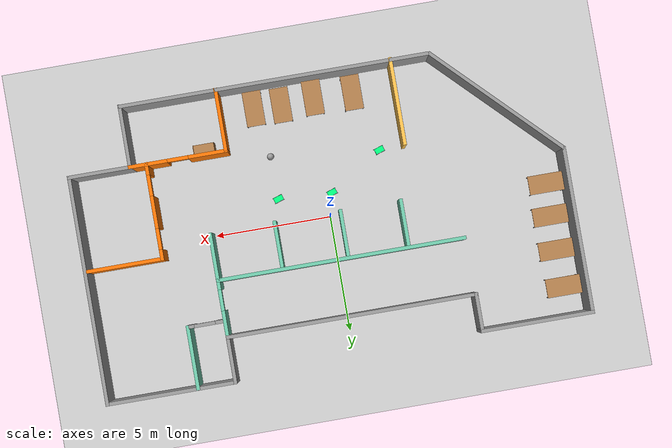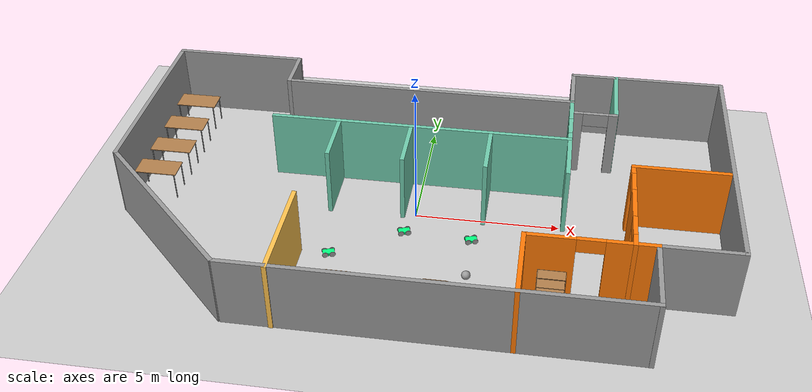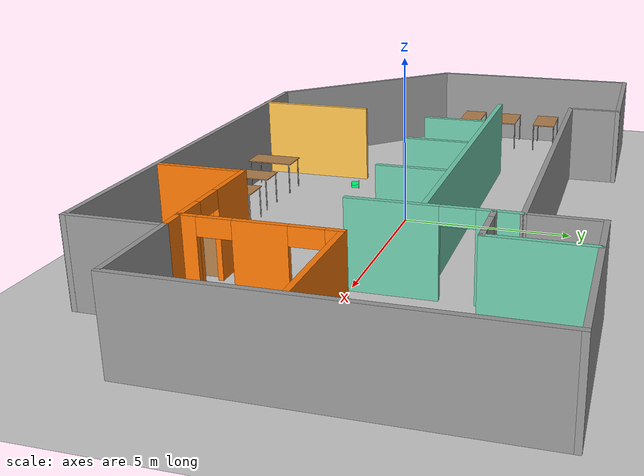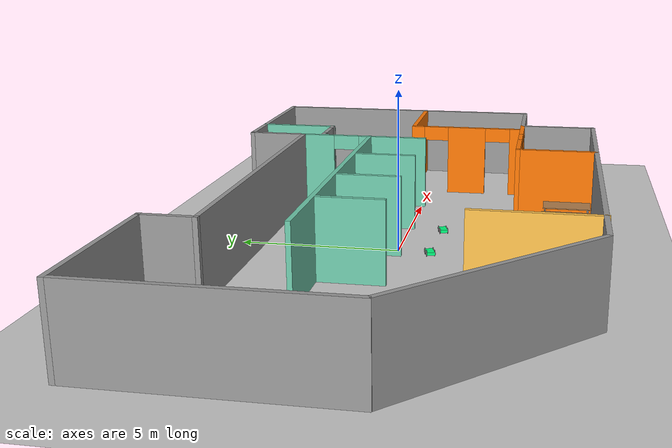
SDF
<sdf version="1.6">
 <world name="default">
  <light name="sun" type="directional">
   <pose>0 0 10 0 -0 0</pose>
   <diffuse>0.8 0.8 0.8 1</diffuse>
   <specular>0.2 0.2 0.2 1</specular>
   <attenuation>
    <range>1000</range>
    <constant>0.9</constant>
    <linear>0.01</linear>
    <quadratic>0.001</quadratic>
   </attenuation>
   <direction>-0.5 0.1 -0.9</direction>
  </light>
  <model name="ground_plane">
   <static>1</static>
   <link name="link">
    <collision name="collision">
     <geometry><plane><normal>0 0 1</normal><size>100 100</size></plane></geometry>
     <surface><friction><ode><mu>100</mu><mu2>50</mu2></ode></friction></surface>
    </collision>
    <visual name="visual">
     <cast_shadows>0</cast_shadows>
     <geometry><plane><normal>0 0 1</normal><size>100 100</size></plane></geometry>
     <material>
      <script><uri>file://media/materials/scripts/gazebo.material</uri><name>Gazebo/Grey</name></script>
     </material>
    </visual>
   </link>
  </model>
  <gravity>0 0 -9.8</gravity>
  <magnetic_field>6e-06 2.3e-05 -4.2e-05</magnetic_field>
  <atmosphere type="adiabatic"/>
  <physics name="default_physics" default="0" type="ode">
   <max_step_size>0.001</max_step_size>
   <real_time_factor>1</real_time_factor>
   <real_time_update_rate>1000</real_time_update_rate>
  </physics>
  <scene><ambient>0.4 0.4 0.4 1</ambient><background>0.7 0.7 0.7 1</background><shadows>1</shadows></scene>
  <spherical_coordinates>
   <surface_model>EARTH_WGS84</surface_model>
   <latitude_deg>0</latitude_deg>
   <longitude_deg>0</longitude_deg>
   <elevation>0</elevation>
   <heading_deg>0</heading_deg>
  </spherical_coordinates>
  <model name="table">
   <static>1</static>
   <link name="link">
    <collision name="surface">
     <pose>0 0 1 0 -0 0</pose>
     <geometry><box><size>1.5 0.8 0.03</size></box></geometry>
     <surface><friction><ode><mu>0.6</mu><mu2>0.6</mu2></ode></friction></surface>
    </collision>
    <visual name="visual1">
     <pose>0 0 1 0 -0 0</pose>
     <geometry><box><size>1.5 0.8 0.03</size></box></geometry>
     <material>
      <script><uri>file://media/materials/scripts/gazebo.material</uri><name>Gazebo/Wood</name></script>
     </material>
    </visual>
    <collision name="front_left_leg">
     <pose>0.68 0.38 0.5 0 -0 0</pose>
     <geometry><cylinder><radius>0.02</radius><length>1</length></cylinder></geometry>
    </collision>
    <visual name="front_left_leg">
     <pose>0.68 0.38 0.5 0 -0 0</pose>
     <geometry><cylinder><radius>0.02</radius><length>1</length></cylinder></geometry>
     <material>
      <script><uri>file://media/materials/scripts/gazebo.material</uri><name>Gazebo/Grey</name></script>
     </material>
    </visual>
    <collision name="front_right_leg">
     <pose>0.68 -0.38 0.5 0 -0 0</pose>
     <geometry><cylinder><radius>0.02</radius><length>1</length></cylinder></geometry>
    </collision>
    <visual name="front_right_leg">
     <pose>0.68 -0.38 0.5 0 -0 0</pose>
     <geometry><cylinder><radius>0.02</radius><length>1</length></cylinder></geometry>
     <material>
      <script><uri>file://media/materials/scripts/gazebo.material</uri><name>Gazebo/Grey</name></script>
     </material>
    </visual>
    <collision name="back_right_leg">
     <pose>-0.68 -0.38 0.5 0 -0 0</pose>
     <geometry><cylinder><radius>0.02</radius><length>1</length></cylinder></geometry>
    </collision>
    <visual name="back_right_leg">
     <pose>-0.68 -0.38 0.5 0 -0 0</pose>
     <geometry><cylinder><radius>0.02</radius><length>1</length></cylinder></geometry>
     <material>
      <script><uri>file://media/materials/scripts/gazebo.material</uri><name>Gazebo/Grey</name></script>
     </material>
    </visual>
    <collision name="back_left_leg">
     <pose>-0.68 0.38 0.5 0 -0 0</pose>
     <geometry><cylinder><radius>0.02</radius><length>1</length></cylinder></geometry>
    </collision>
    <visual name="back_left_leg">
     <pose>-0.68 0.38 0.5 0 -0 0</pose>
     <geometry><cylinder><radius>0.02</radius><length>1</length></cylinder></geometry>
     <material>
      <script><uri>file://media/materials/scripts/gazebo.material</uri><name>Gazebo/Grey</name></script>
     </material>
    </visual>
   </link>
   <pose>-9.31337 4.66156 0 0 -0 0</pose>
  </model>
  <model name="table_clone">
   <static>1</static>
   <link name="link">
    <collision name="surface">
     <pose>0 0 1 0 -0 0</pose>
     <geometry><box><size>1.5 0.8 0.03</size></box></geometry>
     <surface><friction><ode><mu>0.6</mu><mu2>0.6</mu2></ode></friction></surface>
    </collision>
    <visual name="visual1">
     <pose>0 0 1 0 -0 0</pose>
     <geometry><box><size>1.5 0.8 0.03</size></box></geometry>
     <material>
      <script><uri>file://media/materials/scripts/gazebo.material</uri><name>Gazebo/Wood</name></script>
     </material>
    </visual>
    <collision name="front_left_leg">
     <pose>0.68 0.38 0.5 0 -0 0</pose>
     <geometry><cylinder><radius>0.02</radius><length>1</length></cylinder></geometry>
    </collision>
    <visual name="front_left_leg">
     <pose>0.68 0.38 0.5 0 -0 0</pose>
     <geometry><cylinder><radius>0.02</radius><length>1</length></cylinder></geometry>
     <material>
      <script><uri>file://media/materials/scripts/gazebo.material</uri><name>Gazebo/Grey</name></script>
     </material>
    </visual>
    <collision name="front_right_leg">
     <pose>0.68 -0.38 0.5 0 -0 0</pose>
     <geometry><cylinder><radius>0.02</radius><length>1</length></cylinder></geometry>
    </collision>
    <visual name="front_right_leg">
     <pose>0.68 -0.38 0.5 0 -0 0</pose>
     <geometry><cylinder><radius>0.02</radius><length>1</length></cylinder></geometry>
     <material>
      <script><uri>file://media/materials/scripts/gazebo.material</uri><name>Gazebo/Grey</name></script>
     </material>
    </visual>
    <collision name="back_right_leg">
     <pose>-0.68 -0.38 0.5 0 -0 0</pose>
     <geometry><cylinder><radius>0.02</radius><length>1</length></cylinder></geometry>
    </collision>
    <visual name="back_right_leg">
     <pose>-0.68 -0.38 0.5 0 -0 0</pose>
     <geometry><cylinder><radius>0.02</radius><length>1</length></cylinder></geometry>
     <material>
      <script><uri>file://media/materials/scripts/gazebo.material</uri><name>Gazebo/Grey</name></script>
     </material>
    </visual>
    <collision name="back_left_leg">
     <pose>-0.68 0.38 0.5 0 -0 0</pose>
     <geometry><cylinder><radius>0.02</radius><length>1</length></cylinder></geometry>
    </collision>
    <visual name="back_left_leg">
     <pose>-0.68 0.38 0.5 0 -0 0</pose>
     <geometry><cylinder><radius>0.02</radius><length>1</length></cylinder></geometry>
     <material>
      <script><uri>file://media/materials/scripts/gazebo.material</uri><name>Gazebo/Grey</name></script>
     </material>
    </visual>
   </link>
   <pose>-9.2685 3.06963 0 0 -0 0</pose>
  </model>
  <model name="table_clone_0">
   <static>1</static>
   <link name="link">
    <collision name="surface">
     <pose>0 0 1 0 -0 0</pose>
     <geometry><box><size>1.5 0.8 0.03</size></box></geometry>
     <surface><friction><ode><mu>0.6</mu><mu2>0.6</mu2></ode></friction></surface>
    </collision>
    <visual name="visual1">
     <pose>0 0 1 0 -0 0</pose>
     <geometry><box><size>1.5 0.8 0.03</size></box></geometry>
     <material>
      <script><uri>file://media/materials/scripts/gazebo.material</uri><name>Gazebo/Wood</name></script>
     </material>
    </visual>
    <collision name="front_left_leg">
     <pose>0.68 0.38 0.5 0 -0 0</pose>
     <geometry><cylinder><radius>0.02</radius><length>1</length></cylinder></geometry>
    </collision>
    <visual name="front_left_leg">
     <pose>0.68 0.38 0.5 0 -0 0</pose>
     <geometry><cylinder><radius>0.02</radius><length>1</length></cylinder></geometry>
     <material>
      <script><uri>file://media/materials/scripts/gazebo.material</uri><name>Gazebo/Grey</name></script>
     </material>
    </visual>
    <collision name="front_right_leg">
     <pose>0.68 -0.38 0.5 0 -0 0</pose>
     <geometry><cylinder><radius>0.02</radius><length>1</length></cylinder></geometry>
    </collision>
    <visual name="front_right_leg">
     <pose>0.68 -0.38 0.5 0 -0 0</pose>
     <geometry><cylinder><radius>0.02</radius><length>1</length></cylinder></geometry>
     <material>
      <script><uri>file://media/materials/scripts/gazebo.material</uri><name>Gazebo/Grey</name></script>
     </material>
    </visual>
    <collision name="back_right_leg">
     <pose>-0.68 -0.38 0.5 0 -0 0</pose>
     <geometry><cylinder><radius>0.02</radius><length>1</length></cylinder></geometry>
    </collision>
    <visual name="back_right_leg">
     <pose>-0.68 -0.38 0.5 0 -0 0</pose>
     <geometry><cylinder><radius>0.02</radius><length>1</length></cylinder></geometry>
     <material>
      <script><uri>file://media/materials/scripts/gazebo.material</uri><name>Gazebo/Grey</name></script>
     </material>
    </visual>
    <collision name="back_left_leg">
     <pose>-0.68 0.38 0.5 0 -0 0</pose>
     <geometry><cylinder><radius>0.02</radius><length>1</length></cylinder></geometry>
    </collision>
    <visual name="back_left_leg">
     <pose>-0.68 0.38 0.5 0 -0 0</pose>
     <geometry><cylinder><radius>0.02</radius><length>1</length></cylinder></geometry>
     <material>
      <script><uri>file://media/materials/scripts/gazebo.material</uri><name>Gazebo/Grey</name></script>
     </material>
    </visual>
   </link>
   <pose>-9.27088 1.58718 0 0 -0 0</pose>
  </model>
  <model name="table_clone_1">
   <static>1</static>
   <link name="link">
    <collision name="surface">
     <pose>0 0 1 0 -0 0</pose>
     <geometry><box><size>1.5 0.8 0.03</size></box></geometry>
     <surface><friction><ode><mu>0.6</mu><mu2>0.6</mu2></ode></friction></surface>
    </collision>
    <visual name="visual1">
     <pose>0 0 1 0 -0 0</pose>
     <geometry><box><size>1.5 0.8 0.03</size></box></geometry>
     <material>
      <script><uri>file://media/materials/scripts/gazebo.material</uri><name>Gazebo/Wood</name></script>
     </material>
    </visual>
    <collision name="front_left_leg">
     <pose>0.68 0.38 0.5 0 -0 0</pose>
     <geometry><cylinder><radius>0.02</radius><length>1</length></cylinder></geometry>
    </collision>
    <visual name="front_left_leg">
     <pose>0.68 0.38 0.5 0 -0 0</pose>
     <geometry><cylinder><radius>0.02</radius><length>1</length></cylinder></geometry>
     <material>
      <script><uri>file://media/materials/scripts/gazebo.material</uri><name>Gazebo/Grey</name></script>
     </material>
    </visual>
    <collision name="front_right_leg">
     <pose>0.68 -0.38 0.5 0 -0 0</pose>
     <geometry><cylinder><radius>0.02</radius><length>1</length></cylinder></geometry>
    </collision>
    <visual name="front_right_leg">
     <pose>0.68 -0.38 0.5 0 -0 0</pose>
     <geometry><cylinder><radius>0.02</radius><length>1</length></cylinder></geometry>
     <material>
      <script><uri>file://media/materials/scripts/gazebo.material</uri><name>Gazebo/Grey</name></script>
     </material>
    </visual>
    <collision name="back_right_leg">
     <pose>-0.68 -0.38 0.5 0 -0 0</pose>
     <geometry><cylinder><radius>0.02</radius><length>1</length></cylinder></geometry>
    </collision>
    <visual name="back_right_leg">
     <pose>-0.68 -0.38 0.5 0 -0 0</pose>
     <geometry><cylinder><radius>0.02</radius><length>1</length></cylinder></geometry>
     <material>
      <script><uri>file://media/materials/scripts/gazebo.material</uri><name>Gazebo/Grey</name></script>
     </material>
    </visual>
    <collision name="back_left_leg">
     <pose>-0.68 0.38 0.5 0 -0 0</pose>
     <geometry><cylinder><radius>0.02</radius><length>1</length></cylinder></geometry>
    </collision>
    <visual name="back_left_leg">
     <pose>-0.68 0.38 0.5 0 -0 0</pose>
     <geometry><cylinder><radius>0.02</radius><length>1</length></cylinder></geometry>
     <material>
      <script><uri>file://media/materials/scripts/gazebo.material</uri><name>Gazebo/Grey</name></script>
     </material>
    </visual>
   </link>
   <pose>-9.33321 0.190499 0 0 -0 0</pose>
  </model>
  <model name="table_clone_2">
   <static>1</static>
   <link name="link">
    <collision name="surface">
     <pose>0 0 1 0 -0 0</pose>
     <geometry><box><size>1.5 0.8 0.03</size></box></geometry>
     <surface><friction><ode><mu>0.6</mu><mu2>0.6</mu2></ode></friction></surface>
    </collision>
    <visual name="visual1">
     <pose>0 0 1 0 -0 0</pose>
     <geometry><box><size>1.5 0.8 0.03</size></box></geometry>
     <material>
      <script><uri>file://media/materials/scripts/gazebo.material</uri><name>Gazebo/Wood</name></script>
     </material>
    </visual>
    <collision name="front_left_leg">
     <pose>0.68 0.38 0.5 0 -0 0</pose>
     <geometry><cylinder><radius>0.02</radius><length>1</length></cylinder></geometry>
    </collision>
    <visual name="front_left_leg">
     <pose>0.68 0.38 0.5 0 -0 0</pose>
     <geometry><cylinder><radius>0.02</radius><length>1</length></cylinder></geometry>
     <material>
      <script><uri>file://media/materials/scripts/gazebo.material</uri><name>Gazebo/Grey</name></script>
     </material>
    </visual>
    <collision name="front_right_leg">
     <pose>0.68 -0.38 0.5 0 -0 0</pose>
     <geometry><cylinder><radius>0.02</radius><length>1</length></cylinder></geometry>
    </collision>
    <visual name="front_right_leg">
     <pose>0.68 -0.38 0.5 0 -0 0</pose>
     <geometry><cylinder><radius>0.02</radius><length>1</length></cylinder></geometry>
     <material>
      <script><uri>file://media/materials/scripts/gazebo.material</uri><name>Gazebo/Grey</name></script>
     </material>
    </visual>
    <collision name="back_right_leg">
     <pose>-0.68 -0.38 0.5 0 -0 0</pose>
     <geometry><cylinder><radius>0.02</radius><length>1</length></cylinder></geometry>
    </collision>
    <visual name="back_right_leg">
     <pose>-0.68 -0.38 0.5 0 -0 0</pose>
     <geometry><cylinder><radius>0.02</radius><length>1</length></cylinder></geometry>
     <material>
      <script><uri>file://media/materials/scripts/gazebo.material</uri><name>Gazebo/Grey</name></script>
     </material>
    </visual>
    <collision name="back_left_leg">
     <pose>-0.68 0.38 0.5 0 -0 0</pose>
     <geometry><cylinder><radius>0.02</radius><length>1</length></cylinder></geometry>
    </collision>
    <visual name="back_left_leg">
     <pose>-0.68 0.38 0.5 0 -0 0</pose>
     <geometry><cylinder><radius>0.02</radius><length>1</length></cylinder></geometry>
     <material>
      <script><uri>file://media/materials/scripts/gazebo.material</uri><name>Gazebo/Grey</name></script>
     </material>
    </visual>
   </link>
   <pose>1.28425 -5.05118 0 0 -0 1.5707</pose>
  </model>
  <model name="table_clone_2_clone_0">
   <static>1</static>
   <link name="link">
    <collision name="surface">
     <pose>0 0 1 0 -0 0</pose>
     <geometry><box><size>1.5 0.8 0.03</size></box></geometry>
     <surface><friction><ode><mu>0.6</mu><mu2>0.6</mu2></ode></friction></surface>
    </collision>
    <visual name="visual1">
     <pose>0 0 1 0 -0 0</pose>
     <geometry><box><size>1.5 0.8 0.03</size></box></geometry>
     <material>
      <script><uri>file://media/materials/scripts/gazebo.material</uri><name>Gazebo/Wood</name></script>
     </material>
    </visual>
    <collision name="front_left_leg">
     <pose>0.68 0.38 0.5 0 -0 0</pose>
     <geometry><cylinder><radius>0.02</radius><length>1</length></cylinder></geometry>
    </collision>
    <visual name="front_left_leg">
     <pose>0.68 0.38 0.5 0 -0 0</pose>
     <geometry><cylinder><radius>0.02</radius><length>1</length></cylinder></geometry>
     <material>
      <script><uri>file://media/materials/scripts/gazebo.material</uri><name>Gazebo/Grey</name></script>
     </material>
    </visual>
    <collision name="front_right_leg">
     <pose>0.68 -0.38 0.5 0 -0 0</pose>
     <geometry><cylinder><radius>0.02</radius><length>1</length></cylinder></geometry>
    </collision>
    <visual name="front_right_leg">
     <pose>0.68 -0.38 0.5 0 -0 0</pose>
     <geometry><cylinder><radius>0.02</radius><length>1</length></cylinder></geometry>
     <material>
      <script><uri>file://media/materials/scripts/gazebo.material</uri><name>Gazebo/Grey</name></script>
     </material>
    </visual>
    <collision name="back_right_leg">
     <pose>-0.68 -0.38 0.5 0 -0 0</pose>
     <geometry><cylinder><radius>0.02</radius><length>1</length></cylinder></geometry>
    </collision>
    <visual name="back_right_leg">
     <pose>-0.68 -0.38 0.5 0 -0 0</pose>
     <geometry><cylinder><radius>0.02</radius><length>1</length></cylinder></geometry>
     <material>
      <script><uri>file://media/materials/scripts/gazebo.material</uri><name>Gazebo/Grey</name></script>
     </material>
    </visual>
    <collision name="back_left_leg">
     <pose>-0.68 0.38 0.5 0 -0 0</pose>
     <geometry><cylinder><radius>0.02</radius><length>1</length></cylinder></geometry>
    </collision>
    <visual name="back_left_leg">
     <pose>-0.68 0.38 0.5 0 -0 0</pose>
     <geometry><cylinder><radius>0.02</radius><length>1</length></cylinder></geometry>
     <material>
      <script><uri>file://media/materials/scripts/gazebo.material</uri><name>Gazebo/Grey</name></script>
     </material>
    </visual>
   </link>
   <pose>-1.80831 -5.06741 0 0 -0 1.5707</pose>
  </model>
  <model name="table_clone_2_clone_1_clone">
   <static>1</static>
   <link name="link">
    <collision name="surface">
     <pose>0 0 1 0 -0 0</pose>
     <geometry><box><size>1.5 0.8 0.03</size></box></geometry>
     <surface><friction><ode><mu>0.6</mu><mu2>0.6</mu2></ode></friction></surface>
    </collision>
    <visual name="visual1">
     <pose>0 0 1 0 -0 0</pose>
     <geometry><box><size>1.5 0.8 0.03</size></box></geometry>
     <material>
      <script><uri>file://media/materials/scripts/gazebo.material</uri><name>Gazebo/Wood</name></script>
     </material>
    </visual>
    <collision name="front_left_leg">
     <pose>0.68 0.38 0.5 0 -0 0</pose>
     <geometry><cylinder><radius>0.02</radius><length>1</length></cylinder></geometry>
    </collision>
    <visual name="front_left_leg">
     <pose>0.68 0.38 0.5 0 -0 0</pose>
     <geometry><cylinder><radius>0.02</radius><length>1</length></cylinder></geometry>
     <material>
      <script><uri>file://media/materials/scripts/gazebo.material</uri><name>Gazebo/Grey</name></script>
     </material>
    </visual>
    <collision name="front_right_leg">
     <pose>0.68 -0.38 0.5 0 -0 0</pose>
     <geometry><cylinder><radius>0.02</radius><length>1</length></cylinder></geometry>
    </collision>
    <visual name="front_right_leg">
     <pose>0.68 -0.38 0.5 0 -0 0</pose>
     <geometry><cylinder><radius>0.02</radius><length>1</length></cylinder></geometry>
     <material>
      <script><uri>file://media/materials/scripts/gazebo.material</uri><name>Gazebo/Grey</name></script>
     </material>
    </visual>
    <collision name="back_right_leg">
     <pose>-0.68 -0.38 0.5 0 -0 0</pose>
     <geometry><cylinder><radius>0.02</radius><length>1</length></cylinder></geometry>
    </collision>
    <visual name="back_right_leg">
     <pose>-0.68 -0.38 0.5 0 -0 0</pose>
     <geometry><cylinder><radius>0.02</radius><length>1</length></cylinder></geometry>
     <material>
      <script><uri>file://media/materials/scripts/gazebo.material</uri><name>Gazebo/Grey</name></script>
     </material>
    </visual>
    <collision name="back_left_leg">
     <pose>-0.68 0.38 0.5 0 -0 0</pose>
     <geometry><cylinder><radius>0.02</radius><length>1</length></cylinder></geometry>
    </collision>
    <visual name="back_left_leg">
     <pose>-0.68 0.38 0.5 0 -0 0</pose>
     <geometry><cylinder><radius>0.02</radius><length>1</length></cylinder></geometry>
     <material>
      <script><uri>file://media/materials/scripts/gazebo.material</uri><name>Gazebo/Grey</name></script>
     </material>
    </visual>
   </link>
   <pose>-0.118114 -5.13382 0 0 -0 1.5707</pose>
  </model>
  <model name="table_clone_2_clone_1_clone_0">
   <static>1</static>
   <link name="link">
    <collision name="surface">
     <pose>0 0 1 0 -0 0</pose>
     <geometry><box><size>1.5 0.8 0.03</size></box></geometry>
     <surface><friction><ode><mu>0.6</mu><mu2>0.6</mu2></ode></friction></surface>
    </collision>
    <visual name="visual1">
     <pose>0 0 1 0 -0 0</pose>
     <geometry><box><size>1.5 0.8 0.03</size></box></geometry>
     <material>
      <script><uri>file://media/materials/scripts/gazebo.material</uri><name>Gazebo/Wood</name></script>
     </material>
    </visual>
    <collision name="front_left_leg">
     <pose>0.68 0.38 0.5 0 -0 0</pose>
     <geometry><cylinder><radius>0.02</radius><length>1</length></cylinder></geometry>
    </collision>
    <visual name="front_left_leg">
     <pose>0.68 0.38 0.5 0 -0 0</pose>
     <geometry><cylinder><radius>0.02</radius><length>1</length></cylinder></geometry>
     <material>
      <script><uri>file://media/materials/scripts/gazebo.material</uri><name>Gazebo/Grey</name></script>
     </material>
    </visual>
    <collision name="front_right_leg">
     <pose>0.68 -0.38 0.5 0 -0 0</pose>
     <geometry><cylinder><radius>0.02</radius><length>1</length></cylinder></geometry>
    </collision>
    <visual name="front_right_leg">
     <pose>0.68 -0.38 0.5 0 -0 0</pose>
     <geometry><cylinder><radius>0.02</radius><length>1</length></cylinder></geometry>
     <material>
      <script><uri>file://media/materials/scripts/gazebo.material</uri><name>Gazebo/Grey</name></script>
     </material>
    </visual>
    <collision name="back_right_leg">
     <pose>-0.68 -0.38 0.5 0 -0 0</pose>
     <geometry><cylinder><radius>0.02</radius><length>1</length></cylinder></geometry>
    </collision>
    <visual name="back_right_leg">
     <pose>-0.68 -0.38 0.5 0 -0 0</pose>
     <geometry><cylinder><radius>0.02</radius><length>1</length></cylinder></geometry>
     <material>
      <script><uri>file://media/materials/scripts/gazebo.material</uri><name>Gazebo/Grey</name></script>
     </material>
    </visual>
    <collision name="back_left_leg">
     <pose>-0.68 0.38 0.5 0 -0 0</pose>
     <geometry><cylinder><radius>0.02</radius><length>1</length></cylinder></geometry>
    </collision>
    <visual name="back_left_leg">
     <pose>-0.68 0.38 0.5 0 -0 0</pose>
     <geometry><cylinder><radius>0.02</radius><length>1</length></cylinder></geometry>
     <material>
      <script><uri>file://media/materials/scripts/gazebo.material</uri><name>Gazebo/Grey</name></script>
     </material>
    </visual>
   </link>
   <pose>2.45786 -5.09881 0 0 -0 1.5707</pose>
  </model>
  <model name="Diff_Drive_Robot">
   <link name="link_1">
    <pose>0 0 0.025 0 -0 0</pose>
    <inertial>
     <mass>1</mass>
     <inertia>
      <ixx>0.166667</ixx>
      <ixy>0</ixy>
      <ixz>0</ixz>
      <iyy>0.166667</iyy>
      <iyz>0</iyz>
      <izz>0.166667</izz>
     </inertia>
    </inertial>
    <visual name="visual">
     <geometry><box><size>0.4 0.25 0.1</size></box></geometry>
     <material>
      <lighting>1</lighting>
      <script><uri>file://media/materials/scripts/gazebo.material</uri><name>Gazebo/Grey</name></script>
      <shader type="pixel"><normal_map>__default__</normal_map></shader>
      <ambient>0 1 0.5 1</ambient>
      <diffuse>0.7 0.7 0.7 1</diffuse>
      <specular>0.01 0.01 0.01 1</specular>
      <emissive>0 0 0 1</emissive>
     </material>
    </visual>
    <collision name="collision">
     <geometry><box><size>0.4 0.25 0.1</size></box></geometry>
     <surface>
      <friction>
       <ode><mu>1</mu><mu2>1</mu2><fdir1>0 0 0</fdir1><slip1>0</slip1><slip2>0</slip2></ode>
       <torsional>
        <coefficient>1</coefficient>
        <patch_radius>0</patch_radius>
        <surface_radius>0</surface_radius>
        <use_patch_radius>1</use_patch_radius>
        <ode><slip>0</slip></ode>
       </torsional>
      </friction>
      <bounce><restitution_coefficient>0</restitution_coefficient><threshold>1e+06</threshold></bounce>
      <contact>
       <collide_without_contact>0</collide_without_contact>
       <collide_without_contact_bitmask>1</collide_without_contact_bitmask>
       <collide_bitmask>1</collide_bitmask>
       <ode>
        <soft_cfm>0</soft_cfm>
        <soft_erp>0.2</soft_erp>
        <kp>1e+13</kp>
        <kd>1</kd>
        <max_vel>0.01</max_vel>
        <min_depth>0</min_depth>
       </ode>
       <bullet>
        <split_impulse>1</split_impulse>
        <split_impulse_penetration_threshold>-0.01</split_impulse_penetration_threshold>
        <soft_cfm>0</soft_cfm>
        <soft_erp>0.2</soft_erp>
        <kp>1e+13</kp>
        <kd>1</kd>
       </bullet>
      </contact>
     </surface>
    </collision>
   </link>
   <link name="link_2">
    <pose>0.125 0.125 0.025 1.5707 -0 0</pose>
    <inertial>
     <mass>1</mass>
     <inertia><ixx>0.145833</ixx><ixy>0</ixy><ixz>0</ixz><iyy>0.145833</iyy><iyz>0</iyz><izz>0.125</izz></inertia>
    </inertial>
    <visual name="visual">
     <geometry><cylinder><radius>0.1</radius><length>0.01</length></cylinder></geometry>
     <material>
      <lighting>1</lighting>
      <script><uri>file://media/materials/scripts/gazebo.material</uri><name>Gazebo/Grey</name></script>
      <shader type="pixel"><normal_map>__default__</normal_map></shader>
      <ambient>0.3 0.3 0.3 1</ambient>
      <diffuse>0.7 0.7 0.7 1</diffuse>
      <specular>0.01 0.01 0.01 1</specular>
      <emissive>0 0 0 1</emissive>
     </material>
    </visual>
    <collision name="collision">
     <geometry><cylinder><radius>0.1</radius><length>0.01</length></cylinder></geometry>
     <surface>
      <friction>
       <ode><mu>1</mu><mu2>1</mu2><fdir1>0 0 0</fdir1><slip1>0</slip1><slip2>0</slip2></ode>
       <torsional>
        <coefficient>1</coefficient>
        <patch_radius>0</patch_radius>
        <surface_radius>0</surface_radius>
        <use_patch_radius>1</use_patch_radius>
        <ode><slip>0</slip></ode>
       </torsional>
      </friction>
      <bounce><restitution_coefficient>0</restitution_coefficient><threshold>1e+06</threshold></bounce>
      <contact>
       <collide_without_contact>0</collide_without_contact>
       <collide_without_contact_bitmask>1</collide_without_contact_bitmask>
       <collide_bitmask>1</collide_bitmask>
       <ode>
        <soft_cfm>0</soft_cfm>
        <soft_erp>0.2</soft_erp>
        <kp>1e+13</kp>
        <kd>1</kd>
        <max_vel>0.01</max_vel>
        <min_depth>0</min_depth>
       </ode>
       <bullet>
        <split_impulse>1</split_impulse>
        <split_impulse_penetration_threshold>-0.01</split_impulse_penetration_threshold>
        <soft_cfm>0</soft_cfm>
        <soft_erp>0.2</soft_erp>
        <kp>1e+13</kp>
        <kd>1</kd>
       </bullet>
      </contact>
     </surface>
    </collision>
   </link>
   <link name="link_2_clone">
    <pose>0.125 -0.125 0.025 1.5707 -0 0</pose>
    <inertial>
     <mass>1</mass>
     <inertia><ixx>0.145833</ixx><ixy>0</ixy><ixz>0</ixz><iyy>0.145833</iyy><iyz>0</iyz><izz>0.125</izz></inertia>
    </inertial>
    <visual name="visual">
     <geometry><cylinder><radius>0.1</radius><length>0.01</length></cylinder></geometry>
     <material>
      <lighting>1</lighting>
      <script><uri>file://media/materials/scripts/gazebo.material</uri><name>Gazebo/Grey</name></script>
      <shader type="pixel"><normal_map>__default__</normal_map></shader>
      <ambient>0.3 0.3 0.3 1</ambient>
      <diffuse>0.7 0.7 0.7 1</diffuse>
      <specular>0.01 0.01 0.01 1</specular>
      <emissive>0 0 0 1</emissive>
     </material>
    </visual>
    <collision name="collision">
     <geometry><cylinder><radius>0.1</radius><length>0.01</length></cylinder></geometry>
     <surface>
      <friction>
       <ode><mu>1</mu><mu2>1</mu2><fdir1>0 0 0</fdir1><slip1>0</slip1><slip2>0</slip2></ode>
       <torsional>
        <coefficient>1</coefficient>
        <patch_radius>0</patch_radius>
        <surface_radius>0</surface_radius>
        <use_patch_radius>1</use_patch_radius>
        <ode><slip>0</slip></ode>
       </torsional>
      </friction>
      <bounce><restitution_coefficient>0</restitution_coefficient><threshold>1e+06</threshold></bounce>
      <contact>
       <collide_without_contact>0</collide_without_contact>
       <collide_without_contact_bitmask>1</collide_without_contact_bitmask>
       <collide_bitmask>1</collide_bitmask>
       <ode>
        <soft_cfm>0</soft_cfm>
        <soft_erp>0.2</soft_erp>
        <kp>1e+13</kp>
        <kd>1</kd>
        <max_vel>0.01</max_vel>
        <min_depth>0</min_depth>
       </ode>
       <bullet>
        <split_impulse>1</split_impulse>
        <split_impulse_penetration_threshold>-0.01</split_impulse_penetration_threshold>
        <soft_cfm>0</soft_cfm>
        <soft_erp>0.2</soft_erp>
        <kp>1e+13</kp>
        <kd>1</kd>
       </bullet>
      </contact>
     </surface>
    </collision>
   </link>
   <link name="link_2_clone_0">
    <pose>-0.125 0.125 0.025 1.5707 -0 0</pose>
    <inertial>
     <mass>1</mass>
     <inertia><ixx>0.145833</ixx><ixy>0</ixy><ixz>0</ixz><iyy>0.145833</iyy><iyz>0</iyz><izz>0.125</izz></inertia>
    </inertial>
    <visual name="visual">
     <geometry><cylinder><radius>0.1</radius><length>0.01</length></cylinder></geometry>
     <material>
      <lighting>1</lighting>
      <script><uri>file://media/materials/scripts/gazebo.material</uri><name>Gazebo/Grey</name></script>
      <shader type="pixel"><normal_map>__default__</normal_map></shader>
      <ambient>0.3 0.3 0.3 1</ambient>
      <diffuse>0.7 0.7 0.7 1</diffuse>
      <specular>0.01 0.01 0.01 1</specular>
      <emissive>0 0 0 1</emissive>
     </material>
    </visual>
    <collision name="collision">
     <geometry><cylinder><radius>0.1</radius><length>0.01</length></cylinder></geometry>
     <surface>
      <friction>
       <ode><mu>1</mu><mu2>1</mu2><fdir1>0 0 0</fdir1><slip1>0</slip1><slip2>0</slip2></ode>
       <torsional>
        <coefficient>1</coefficient>
        <patch_radius>0</patch_radius>
        <surface_radius>0</surface_radius>
        <use_patch_radius>1</use_patch_radius>
        <ode><slip>0</slip></ode>
       </torsional>
      </friction>
      <bounce><restitution_coefficient>0</restitution_coefficient><threshold>1e+06</threshold></bounce>
      <contact>
       <collide_without_contact>0</collide_without_contact>
       <collide_without_contact_bitmask>1</collide_without_contact_bitmask>
       <collide_bitmask>1</collide_bitmask>
       <ode>
        <soft_cfm>0</soft_cfm>
        <soft_erp>0.2</soft_erp>
        <kp>1e+13</kp>
        <kd>1</kd>
        <max_vel>0.01</max_vel>
        <min_depth>0</min_depth>
       </ode>
       <bullet>
        <split_impulse>1</split_impulse>
        <split_impulse_penetration_threshold>-0.01</split_impulse_penetration_threshold>
        <soft_cfm>0</soft_cfm>
        <soft_erp>0.2</soft_erp>
        <kp>1e+13</kp>
        <kd>1</kd>
       </bullet>
      </contact>
     </surface>
    </collision>
   </link>
   <link name="link_2_clone_1">
    <pose>-0.125 -0.125 0.025 1.5707 -0 0</pose>
    <inertial>
     <mass>1</mass>
     <inertia><ixx>0.145833</ixx><ixy>0</ixy><ixz>0</ixz><iyy>0.145833</iyy><iyz>0</iyz><izz>0.125</izz></inertia>
    </inertial>
    <visual name="visual">
     <geometry><cylinder><radius>0.1</radius><length>0.01</length></cylinder></geometry>
     <material>
      <lighting>1</lighting>
      <script><uri>file://media/materials/scripts/gazebo.material</uri><name>Gazebo/Grey</name></script>
      <shader type="pixel"><normal_map>__default__</normal_map></shader>
      <ambient>0.3 0.3 0.3 1</ambient>
      <diffuse>0.7 0.7 0.7 1</diffuse>
      <specular>0.01 0.01 0.01 1</specular>
      <emissive>0 0 0 1</emissive>
     </material>
    </visual>
    <collision name="collision">
     <geometry><cylinder><radius>0.1</radius><length>0.01</length></cylinder></geometry>
     <surface>
      <friction>
       <ode><mu>1</mu><mu2>1</mu2><fdir1>0 0 0</fdir1><slip1>0</slip1><slip2>0</slip2></ode>
       <torsional>
        <coefficient>1</coefficient>
        <patch_radius>0</patch_radius>
        <surface_radius>0</surface_radius>
        <use_patch_radius>1</use_patch_radius>
        <ode><slip>0</slip></ode>
       </torsional>
      </friction>
      <bounce><restitution_coefficient>0</restitution_coefficient><threshold>1e+06</threshold></bounce>
      <contact>
       <collide_without_contact>0</collide_without_contact>
       <collide_without_contact_bitmask>1</collide_without_contact_bitmask>
       <collide_bitmask>1</collide_bitmask>
       <ode>
        <soft_cfm>0</soft_cfm>
        <soft_erp>0.2</soft_erp>
        <kp>1e+13</kp>
        <kd>1</kd>
        <max_vel>0.01</max_vel>
        <min_depth>0</min_depth>
       </ode>
       <bullet>
        <split_impulse>1</split_impulse>
        <split_impulse_penetration_threshold>-0.01</split_impulse_penetration_threshold>
        <soft_cfm>0</soft_cfm>
        <soft_erp>0.2</soft_erp>
        <kp>1e+13</kp>
        <kd>1</kd>
       </bullet>
      </contact>
     </surface>
    </collision>
   </link>
   <joint name="link_1_JOINT_1" type="revolute">
    <parent>link_1</parent>
    <child>link_2</child>
    <axis>
     <xyz>0 0 1</xyz>
     <use_parent_model_frame>0</use_parent_model_frame>
     <limit>
      <lower>-1.79769e+308</lower>
      <upper>1.79769e+308</upper>
      <effort>-1</effort>
      <velocity>-1</velocity>
     </limit>
     <dynamics>
      <spring_reference>0</spring_reference>
      <spring_stiffness>0</spring_stiffness>
      <damping>0</damping>
      <friction>0</friction>
     </dynamics>
     <use_parent_model_frame>1</use_parent_model_frame>
    </axis>
    <physics>
     <ode><limit><cfm>0</cfm><erp>0.2</erp></limit><suspension><cfm>0</cfm><erp>0.2</erp></suspension></ode>
    </physics>
   </joint>
   <joint name="link_1_JOINT_2" type="revolute">
    <parent>link_1</parent>
    <child>link_2_clone</child>
    <axis>
     <xyz>0 0 1</xyz>
     <use_parent_model_frame>0</use_parent_model_frame>
     <limit>
      <lower>-1.79769e+308</lower>
      <upper>1.79769e+308</upper>
      <effort>-1</effort>
      <velocity>-1</velocity>
     </limit>
     <dynamics>
      <spring_reference>0</spring_reference>
      <spring_stiffness>0</spring_stiffness>
      <damping>0</damping>
      <friction>0</friction>
     </dynamics>
     <use_parent_model_frame>1</use_parent_model_frame>
    </axis>
    <physics>
     <ode><limit><cfm>0</cfm><erp>0.2</erp></limit><suspension><cfm>0</cfm><erp>0.2</erp></suspension></ode>
    </physics>
   </joint>
   <joint name="link_1_JOINT_3" type="revolute">
    <parent>link_1</parent>
    <child>link_2_clone_0</child>
    <axis>
     <xyz>0 0 1</xyz>
     <use_parent_model_frame>0</use_parent_model_frame>
     <limit>
      <lower>-1.79769e+308</lower>
      <upper>1.79769e+308</upper>
      <effort>-1</effort>
      <velocity>-1</velocity>
     </limit>
     <dynamics>
      <spring_reference>0</spring_reference>
      <spring_stiffness>0</spring_stiffness>
      <damping>0</damping>
      <friction>0</friction>
     </dynamics>
     <use_parent_model_frame>1</use_parent_model_frame>
    </axis>
    <physics>
     <ode><limit><cfm>0</cfm><erp>0.2</erp></limit><suspension><cfm>0</cfm><erp>0.2</erp></suspension></ode>
    </physics>
   </joint>
   <joint name="link_1_JOINT_4" type="revolute">
    <parent>link_1</parent>
    <child>link_2_clone_1</child>
    <axis>
     <xyz>1 0 0</xyz>
     <use_parent_model_frame>0</use_parent_model_frame>
     <limit>
      <lower>-1.79769e+308</lower>
      <upper>1.79769e+308</upper>
      <effort>-1</effort>
      <velocity>-1</velocity>
     </limit>
     <dynamics>
      <spring_reference>0</spring_reference>
      <spring_stiffness>0</spring_stiffness>
      <damping>0</damping>
      <friction>0</friction>
     </dynamics>
     <use_parent_model_frame>1</use_parent_model_frame>
    </axis>
    <physics>
     <ode><limit><cfm>0</cfm><erp>0.2</erp></limit><suspension><cfm>0</cfm><erp>0.2</erp></suspension></ode>
    </physics>
   </joint>
   <static>0</static>
   <pose>2.08325 -1.13619 0.075 1e-06 -1e-06 0.305181</pose>
  </model>
  <model name="Building">
   <link name="Wall_11">
    <pose>1.2 -6.05 0 0 -0 0</pose>
    <inertial>
     <mass>1</mass>
     <inertia><ixx>1</ixx><ixy>0</ixy><ixz>0</ixz><iyy>1</iyy><iyz>0</iyz><izz>1</izz></inertia>
    </inertial>
    <visual name="Wall_11_Visual">
     <pose>0 0 1.25 0 -0 0</pose>
     <geometry><box><size>13.3 0.15 2.5</size></box></geometry>
     <material>
      <script><uri>file://media/materials/scripts/gazebo.material</uri><name>Gazebo/Grey</name></script>
      <ambient>1 1 1 1</ambient>
      <shader type="pixel"><normal_map>__default__</normal_map></shader>
      <diffuse>0.7 0.7 0.7 1</diffuse>
      <specular>0.01 0.01 0.01 1</specular>
      <emissive>0 0 0 1</emissive>
     </material>
     <meta><layer>0</layer></meta>
    </visual>
    <collision name="Wall_11_Collision">
     <pose>0 0 1.25 0 -0 0</pose>
     <geometry><box><size>13.3 0.15 2.5</size></box></geometry>
     <surface>
      <friction>
       <ode><mu>1</mu><mu2>1</mu2><fdir1>0 0 0</fdir1><slip1>0</slip1><slip2>0</slip2></ode>
       <torsional>
        <coefficient>1</coefficient>
        <patch_radius>0</patch_radius>
        <surface_radius>0</surface_radius>
        <use_patch_radius>1</use_patch_radius>
        <ode><slip>0</slip></ode>
       </torsional>
      </friction>
      <bounce><restitution_coefficient>0</restitution_coefficient><threshold>1e+06</threshold></bounce>
      <contact>
       <collide_without_contact>0</collide_without_contact>
       <collide_without_contact_bitmask>1</collide_without_contact_bitmask>
       <collide_bitmask>1</collide_bitmask>
       <ode>
        <soft_cfm>0</soft_cfm>
        <soft_erp>0.2</soft_erp>
        <kp>1e+13</kp>
        <kd>1</kd>
        <max_vel>0.01</max_vel>
        <min_depth>0</min_depth>
       </ode>
       <bullet>
        <split_impulse>1</split_impulse>
        <split_impulse_penetration_threshold>-0.01</split_impulse_penetration_threshold>
        <soft_cfm>0</soft_cfm>
        <soft_erp>0.2</soft_erp>
        <kp>1e+13</kp>
        <kd>1</kd>
       </bullet>
      </contact>
     </surface>
    </collision>
   </link>
   <link name="Wall_114">
    <pose>5.74685 3.602 0 0 -0 0</pose>
    <visual name="Wall_114_Visual_0">
     <pose>-0.620125 0 1.25 0 -0 0</pose>
     <geometry><box><size>0.409749 0.15 2.5</size></box></geometry>
     <material>
      <script><uri>file://media/materials/scripts/gazebo.material</uri><name>Gazebo/Grey</name></script>
      <ambient>1 1 1 1</ambient>
      <shader type="pixel"/>
      <diffuse>0.7 0.7 0.7 1</diffuse>
      <specular>0.01 0.01 0.01 1</specular>
      <emissive>0 0 0 1</emissive>
     </material>
     <meta><layer>0</layer></meta>
    </visual>
    <visual name="Wall_114_Visual_1">
     <pose>0.654875 0 1.25 0 -0 0</pose>
     <geometry><box><size>0.340251 0.15 2.5</size></box></geometry>
     <material>
      <script><uri>file://media/materials/scripts/gazebo.material</uri><name>Gazebo/Grey</name></script>
      <ambient>1 1 1 1</ambient>
      <shader type="pixel"/>
      <diffuse>0.7 0.7 0.7 1</diffuse>
      <specular>0.01 0.01 0.01 1</specular>
      <emissive>0 0 0 1</emissive>
     </material>
     <meta><layer>0</layer></meta>
    </visual>
    <visual name="Wall_114_Visual_2">
     <pose>0.034749 0 2.25 0 -0 0</pose>
     <geometry><box><size>0.9 0.15 0.5</size></box></geometry>
     <material>
      <script><uri>file://media/materials/scripts/gazebo.material</uri><name>Gazebo/Grey</name></script>
      <ambient>1 1 1 1</ambient>
      <shader type="pixel"/>
      <diffuse>0.7 0.7 0.7 1</diffuse>
      <specular>0.01 0.01 0.01 1</specular>
      <emissive>0 0 0 1</emissive>
     </material>
     <meta><layer>0</layer></meta>
    </visual>
    <collision name="Wall_114_Collision_0">
     <pose>-0.620125 0 1.25 0 -0 0</pose>
     <geometry><box><size>0.409749 0.15 2.5</size></box></geometry>
     <surface>
      <friction>
       <ode><mu>1</mu><mu2>1</mu2><fdir1>0 0 0</fdir1><slip1>0</slip1><slip2>0</slip2></ode>
       <torsional>
        <coefficient>1</coefficient>
        <patch_radius>0</patch_radius>
        <surface_radius>0</surface_radius>
        <use_patch_radius>1</use_patch_radius>
        <ode><slip>0</slip></ode>
       </torsional>
      </friction>
      <bounce><restitution_coefficient>0</restitution_coefficient><threshold>1e+06</threshold></bounce>
      <contact>
       <collide_without_contact>0</collide_without_contact>
       <collide_without_contact_bitmask>1</collide_without_contact_bitmask>
       <collide_bitmask>1</collide_bitmask>
       <ode>
        <soft_cfm>0</soft_cfm>
        <soft_erp>0.2</soft_erp>
        <kp>1e+13</kp>
        <kd>1</kd>
        <max_vel>0.01</max_vel>
        <min_depth>0</min_depth>
       </ode>
       <bullet>
        <split_impulse>1</split_impulse>
        <split_impulse_penetration_threshold>-0.01</split_impulse_penetration_threshold>
        <soft_cfm>0</soft_cfm>
        <soft_erp>0.2</soft_erp>
        <kp>1e+13</kp>
        <kd>1</kd>
       </bullet>
      </contact>
     </surface>
    </collision>
    <collision name="Wall_114_Collision_1">
     <pose>0.654875 0 1.25 0 -0 0</pose>
     <geometry><box><size>0.340251 0.15 2.5</size></box></geometry>
     <surface>
      <friction>
       <ode><mu>1</mu><mu2>1</mu2><fdir1>0 0 0</fdir1><slip1>0</slip1><slip2>0</slip2></ode>
       <torsional>
        <coefficient>1</coefficient>
        <patch_radius>0</patch_radius>
        <surface_radius>0</surface_radius>
        <use_patch_radius>1</use_patch_radius>
        <ode><slip>0</slip></ode>
       </torsional>
      </friction>
      <bounce><restitution_coefficient>0</restitution_coefficient><threshold>1e+06</threshold></bounce>
      <contact>
       <collide_without_contact>0</collide_without_contact>
       <collide_without_contact_bitmask>1</collide_without_contact_bitmask>
       <collide_bitmask>1</collide_bitmask>
       <ode>
        <soft_cfm>0</soft_cfm>
        <soft_erp>0.2</soft_erp>
        <kp>1e+13</kp>
        <kd>1</kd>
        <max_vel>0.01</max_vel>
        <min_depth>0</min_depth>
       </ode>
       <bullet>
        <split_impulse>1</split_impulse>
        <split_impulse_penetration_threshold>-0.01</split_impulse_penetration_threshold>
        <soft_cfm>0</soft_cfm>
        <soft_erp>0.2</soft_erp>
        <kp>1e+13</kp>
        <kd>1</kd>
       </bullet>
      </contact>
     </surface>
    </collision>
    <collision name="Wall_114_Collision_2">
     <pose>0.034749 0 2.25 0 -0 0</pose>
     <geometry><box><size>0.9 0.15 0.5</size></box></geometry>
     <surface>
      <friction>
       <ode><mu>1</mu><mu2>1</mu2><fdir1>0 0 0</fdir1><slip1>0</slip1><slip2>0</slip2></ode>
       <torsional>
        <coefficient>1</coefficient>
        <patch_radius>0</patch_radius>
        <surface_radius>0</surface_radius>
        <use_patch_radius>1</use_patch_radius>
        <ode><slip>0</slip></ode>
       </torsional>
      </friction>
      <bounce><restitution_coefficient>0</restitution_coefficient><threshold>1e+06</threshold></bounce>
      <contact>
       <collide_without_contact>0</collide_without_contact>
       <collide_without_contact_bitmask>1</collide_without_contact_bitmask>
       <collide_bitmask>1</collide_bitmask>
       <ode>
        <soft_cfm>0</soft_cfm>
        <soft_erp>0.2</soft_erp>
        <kp>1e+13</kp>
        <kd>1</kd>
        <max_vel>0.01</max_vel>
        <min_depth>0</min_depth>
       </ode>
       <bullet>
        <split_impulse>1</split_impulse>
        <split_impulse_penetration_threshold>-0.01</split_impulse_penetration_threshold>
        <soft_cfm>0</soft_cfm>
        <soft_erp>0.2</soft_erp>
        <kp>1e+13</kp>
        <kd>1</kd>
       </bullet>
      </contact>
     </surface>
    </collision>
   </link>
   <link name="Wall_116">
    <pose>6.50779 4.9025 0 0 -0 1.5708</pose>
    <visual name="Wall_116_Visual">
     <pose>0 0 1.25 0 -0 0</pose>
     <geometry><box><size>2.75 0.15 2.5</size></box></geometry>
     <material>
      <script><uri>file://media/materials/scripts/gazebo.material</uri><name>Gazebo/Grey</name></script>
      <ambient>0.435294 0.796078 0.67451 1</ambient>
      <shader type="pixel"/>
      <diffuse>0.7 0.7 0.7 1</diffuse>
      <specular>0.01 0.01 0.01 1</specular>
      <emissive>0 0 0 1</emissive>
     </material>
     <meta><layer>0</layer></meta>
    </visual>
    <collision name="Wall_116_Collision">
     <pose>0 0 1.25 0 -0 0</pose>
     <geometry><box><size>2.75 0.15 2.5</size></box></geometry>
     <surface>
      <friction>
       <ode><mu>1</mu><mu2>1</mu2><fdir1>0 0 0</fdir1><slip1>0</slip1><slip2>0</slip2></ode>
       <torsional>
        <coefficient>1</coefficient>
        <patch_radius>0</patch_radius>
        <surface_radius>0</surface_radius>
        <use_patch_radius>1</use_patch_radius>
        <ode><slip>0</slip></ode>
       </torsional>
      </friction>
      <bounce><restitution_coefficient>0</restitution_coefficient><threshold>1e+06</threshold></bounce>
      <contact>
       <collide_without_contact>0</collide_without_contact>
       <collide_without_contact_bitmask>1</collide_without_contact_bitmask>
       <collide_bitmask>1</collide_bitmask>
       <ode>
        <soft_cfm>0</soft_cfm>
        <soft_erp>0.2</soft_erp>
        <kp>1e+13</kp>
        <kd>1</kd>
        <max_vel>0.01</max_vel>
        <min_depth>0</min_depth>
       </ode>
       <bullet>
        <split_impulse>1</split_impulse>
        <split_impulse_penetration_threshold>-0.01</split_impulse_penetration_threshold>
        <soft_cfm>0</soft_cfm>
        <soft_erp>0.2</soft_erp>
        <kp>1e+13</kp>
        <kd>1</kd>
       </bullet>
      </contact>
     </surface>
    </collision>
   </link>
   <link name="Wall_120">
    <pose>7.77481 -4.83428 0 0 -0 1.57077</pose>
    <inertial>
     <mass>1</mass>
     <inertia><ixx>1</ixx><ixy>0</ixy><ixz>0</ixz><iyy>1</iyy><iyz>0</iyz><izz>1</izz></inertia>
    </inertial>
    <visual name="Wall_120_Visual">
     <pose>0 0 1.25 0 -0 0</pose>
     <geometry><box><size>2.6 0.15 2.5</size></box></geometry>
     <material>
      <script><uri>file://media/materials/scripts/gazebo.material</uri><name>Gazebo/Grey</name></script>
      <ambient>1 1 1 1</ambient>
      <shader type="pixel"><normal_map>__default__</normal_map></shader>
      <diffuse>0.7 0.7 0.7 1</diffuse>
      <specular>0.01 0.01 0.01 1</specular>
      <emissive>0 0 0 1</emissive>
     </material>
     <meta><layer>0</layer></meta>
    </visual>
    <collision name="Wall_120_Collision">
     <pose>0 0 1.25 0 -0 0</pose>
     <geometry><box><size>2.6 0.15 2.5</size></box></geometry>
     <surface>
      <friction>
       <ode><mu>1</mu><mu2>1</mu2><fdir1>0 0 0</fdir1><slip1>0</slip1><slip2>0</slip2></ode>
       <torsional>
        <coefficient>1</coefficient>
        <patch_radius>0</patch_radius>
        <surface_radius>0</surface_radius>
        <use_patch_radius>1</use_patch_radius>
        <ode><slip>0</slip></ode>
       </torsional>
      </friction>
      <bounce><restitution_coefficient>0</restitution_coefficient><threshold>1e+06</threshold></bounce>
      <contact>
       <collide_without_contact>0</collide_without_contact>
       <collide_without_contact_bitmask>1</collide_without_contact_bitmask>
       <collide_bitmask>1</collide_bitmask>
       <ode>
        <soft_cfm>0</soft_cfm>
        <soft_erp>0.2</soft_erp>
        <kp>1e+13</kp>
        <kd>1</kd>
        <max_vel>0.01</max_vel>
        <min_depth>0</min_depth>
       </ode>
       <bullet>
        <split_impulse>1</split_impulse>
        <split_impulse_penetration_threshold>-0.01</split_impulse_penetration_threshold>
        <soft_cfm>0</soft_cfm>
        <soft_erp>0.2</soft_erp>
        <kp>1e+13</kp>
        <kd>1</kd>
       </bullet>
      </contact>
     </surface>
    </collision>
   </link>
   <link name="Wall_122">
    <pose>7.07785 -1.4415 0 0 -0 1.5708</pose>
    <visual name="Wall_122_Visual_0">
     <pose>-1.82998 0 1.25 0 -0 0</pose>
     <geometry><box><size>0.532998 0.15 2.5</size></box></geometry>
     <material>
      <script><uri>file://media/materials/scripts/gazebo.material</uri><name>Gazebo/Grey</name></script>
      <ambient>0.996078 0.47451 0.0196078 1</ambient>
      <shader type="pixel"/>
      <diffuse>0.7 0.7 0.7 1</diffuse>
      <specular>0.01 0.01 0.01 1</specular>
      <emissive>0 0 0 1</emissive>
     </material>
     <meta><layer>0</layer></meta>
    </visual>
    <visual name="Wall_122_Visual_1">
     <pose>0.029829 0 1.25 0 -0 0</pose>
     <geometry><box><size>1.38662 0.15 2.5</size></box></geometry>
     <material>
      <script><uri>file://media/materials/scripts/gazebo.material</uri><name>Gazebo/Grey</name></script>
      <ambient>0.996078 0.47451 0.0196078 1</ambient>
      <shader type="pixel"/>
      <diffuse>0.7 0.7 0.7 1</diffuse>
      <specular>0.01 0.01 0.01 1</specular>
      <emissive>0 0 0 1</emissive>
     </material>
     <meta><layer>0</layer></meta>
    </visual>
    <visual name="Wall_122_Visual_2">
     <pose>1.85981 0 1.25 0 -0 0</pose>
     <geometry><box><size>0.473341 0.15 2.5</size></box></geometry>
     <material>
      <script><uri>file://media/materials/scripts/gazebo.material</uri><name>Gazebo/Grey</name></script>
      <ambient>0.996078 0.47451 0.0196078 1</ambient>
      <shader type="pixel"/>
      <diffuse>0.7 0.7 0.7 1</diffuse>
      <specular>0.01 0.01 0.01 1</specular>
      <emissive>0 0 0 1</emissive>
     </material>
     <meta><layer>0</layer></meta>
    </visual>
    <visual name="Wall_122_Visual_3">
     <pose>-1.11348 0 2.25 0 -0 0</pose>
     <geometry><box><size>0.9 0.15 0.5</size></box></geometry>
     <material>
      <script><uri>file://media/materials/scripts/gazebo.material</uri><name>Gazebo/Grey</name></script>
      <ambient>0.996078 0.47451 0.0196078 1</ambient>
      <shader type="pixel"/>
      <diffuse>0.7 0.7 0.7 1</diffuse>
      <specular>0.01 0.01 0.01 1</specular>
      <emissive>0 0 0 1</emissive>
     </material>
     <meta><layer>0</layer></meta>
    </visual>
    <visual name="Wall_122_Visual_4">
     <pose>1.17314 0 2.25 0 -0 0</pose>
     <geometry><box><size>0.9 0.15 0.5</size></box></geometry>
     <material>
      <script><uri>file://media/materials/scripts/gazebo.material</uri><name>Gazebo/Grey</name></script>
      <ambient>0.996078 0.47451 0.0196078 1</ambient>
      <shader type="pixel"/>
      <diffuse>0.7 0.7 0.7 1</diffuse>
      <specular>0.01 0.01 0.01 1</specular>
      <emissive>0 0 0 1</emissive>
     </material>
     <meta><layer>0</layer></meta>
    </visual>
    <collision name="Wall_122_Collision_0">
     <pose>-1.82998 0 1.25 0 -0 0</pose>
     <geometry><box><size>0.532998 0.15 2.5</size></box></geometry>
     <surface>
      <friction>
       <ode><mu>1</mu><mu2>1</mu2><fdir1>0 0 0</fdir1><slip1>0</slip1><slip2>0</slip2></ode>
       <torsional>
        <coefficient>1</coefficient>
        <patch_radius>0</patch_radius>
        <surface_radius>0</surface_radius>
        <use_patch_radius>1</use_patch_radius>
        <ode><slip>0</slip></ode>
       </torsional>
      </friction>
      <bounce><restitution_coefficient>0</restitution_coefficient><threshold>1e+06</threshold></bounce>
      <contact>
       <collide_without_contact>0</collide_without_contact>
       <collide_without_contact_bitmask>1</collide_without_contact_bitmask>
       <collide_bitmask>1</collide_bitmask>
       <ode>
        <soft_cfm>0</soft_cfm>
        <soft_erp>0.2</soft_erp>
        <kp>1e+13</kp>
        <kd>1</kd>
        <max_vel>0.01</max_vel>
        <min_depth>0</min_depth>
       </ode>
       <bullet>
        <split_impulse>1</split_impulse>
        <split_impulse_penetration_threshold>-0.01</split_impulse_penetration_threshold>
        <soft_cfm>0</soft_cfm>
        <soft_erp>0.2</soft_erp>
        <kp>1e+13</kp>
        <kd>1</kd>
       </bullet>
      </contact>
     </surface>
    </collision>
    <collision name="Wall_122_Collision_1">
     <pose>0.029829 0 1.25 0 -0 0</pose>
     <geometry><box><size>1.38662 0.15 2.5</size></box></geometry>
     <surface>
      <friction>
       <ode><mu>1</mu><mu2>1</mu2><fdir1>0 0 0</fdir1><slip1>0</slip1><slip2>0</slip2></ode>
       <torsional>
        <coefficient>1</coefficient>
        <patch_radius>0</patch_radius>
        <surface_radius>0</surface_radius>
        <use_patch_radius>1</use_patch_radius>
        <ode><slip>0</slip></ode>
       </torsional>
      </friction>
      <bounce><restitution_coefficient>0</restitution_coefficient><threshold>1e+06</threshold></bounce>
      <contact>
       <collide_without_contact>0</collide_without_contact>
       <collide_without_contact_bitmask>1</collide_without_contact_bitmask>
       <collide_bitmask>1</collide_bitmask>
       <ode>
        <soft_cfm>0</soft_cfm>
        <soft_erp>0.2</soft_erp>
        <kp>1e+13</kp>
        <kd>1</kd>
        <max_vel>0.01</max_vel>
        <min_depth>0</min_depth>
       </ode>
       <bullet>
        <split_impulse>1</split_impulse>
        <split_impulse_penetration_threshold>-0.01</split_impulse_penetration_threshold>
        <soft_cfm>0</soft_cfm>
        <soft_erp>0.2</soft_erp>
        <kp>1e+13</kp>
        <kd>1</kd>
       </bullet>
      </contact>
     </surface>
    </collision>
    <collision name="Wall_122_Collision_3">
     <pose>-1.11348 0 2.25 0 -0 0</pose>
     <geometry><box><size>0.9 0.15 0.5</size></box></geometry>
     <surface>
      <friction>
       <ode><mu>1</mu><mu2>1</mu2><fdir1>0 0 0</fdir1><slip1>0</slip1><slip2>0</slip2></ode>
       <torsional>
        <coefficient>1</coefficient>
        <patch_radius>0</patch_radius>
        <surface_radius>0</surface_radius>
        <use_patch_radius>1</use_patch_radius>
        <ode><slip>0</slip></ode>
       </torsional>
      </friction>
      <bounce><restitution_coefficient>0</restitution_coefficient><threshold>1e+06</threshold></bounce>
      <contact>
       <collide_without_contact>0</collide_without_contact>
       <collide_without_contact_bitmask>1</collide_without_contact_bitmask>
       <collide_bitmask>1</collide_bitmask>
       <ode>
        <soft_cfm>0</soft_cfm>
        <soft_erp>0.2</soft_erp>
        <kp>1e+13</kp>
        <kd>1</kd>
        <max_vel>0.01</max_vel>
        <min_depth>0</min_depth>
       </ode>
       <bullet>
        <split_impulse>1</split_impulse>
        <split_impulse_penetration_threshold>-0.01</split_impulse_penetration_threshold>
        <soft_cfm>0</soft_cfm>
        <soft_erp>0.2</soft_erp>
        <kp>1e+13</kp>
        <kd>1</kd>
       </bullet>
      </contact>
     </surface>
    </collision>
    <collision name="Wall_122_Collision_2">
     <pose>1.85981 0 1.25 0 -0 0</pose>
     <geometry><box><size>0.473341 0.15 2.5</size></box></geometry>
     <surface>
      <friction>
       <ode><mu>1</mu><mu2>1</mu2><fdir1>0 0 0</fdir1><slip1>0</slip1><slip2>0</slip2></ode>
       <torsional>
        <coefficient>1</coefficient>
        <patch_radius>0</patch_radius>
        <surface_radius>0</surface_radius>
        <use_patch_radius>1</use_patch_radius>
        <ode><slip>0</slip></ode>
       </torsional>
      </friction>
      <bounce><restitution_coefficient>0</restitution_coefficient><threshold>1e+06</threshold></bounce>
      <contact>
       <collide_without_contact>0</collide_without_contact>
       <collide_without_contact_bitmask>1</collide_without_contact_bitmask>
       <collide_bitmask>1</collide_bitmask>
       <ode>
        <soft_cfm>0</soft_cfm>
        <soft_erp>0.2</soft_erp>
        <kp>1e+13</kp>
        <kd>1</kd>
        <max_vel>0.01</max_vel>
        <min_depth>0</min_depth>
       </ode>
       <bullet>
        <split_impulse>1</split_impulse>
        <split_impulse_penetration_threshold>-0.01</split_impulse_penetration_threshold>
        <soft_cfm>0</soft_cfm>
        <soft_erp>0.2</soft_erp>
        <kp>1e+13</kp>
        <kd>1</kd>
       </bullet>
      </contact>
     </surface>
    </collision>
    <collision name="Wall_122_Collision_4">
     <pose>1.17314 0 2.25 0 -0 0</pose>
     <geometry><box><size>0.9 0.15 0.5</size></box></geometry>
     <surface>
      <friction>
       <ode><mu>1</mu><mu2>1</mu2><fdir1>0 0 0</fdir1><slip1>0</slip1><slip2>0</slip2></ode>
       <torsional>
        <coefficient>1</coefficient>
        <patch_radius>0</patch_radius>
        <surface_radius>0</surface_radius>
        <use_patch_radius>1</use_patch_radius>
        <ode><slip>0</slip></ode>
       </torsional>
      </friction>
      <bounce><restitution_coefficient>0</restitution_coefficient><threshold>1e+06</threshold></bounce>
      <contact>
       <collide_without_contact>0</collide_without_contact>
       <collide_without_contact_bitmask>1</collide_without_contact_bitmask>
       <collide_bitmask>1</collide_bitmask>
       <ode>
        <soft_cfm>0</soft_cfm>
        <soft_erp>0.2</soft_erp>
        <kp>1e+13</kp>
        <kd>1</kd>
        <max_vel>0.01</max_vel>
        <min_depth>0</min_depth>
       </ode>
       <bullet>
        <split_impulse>1</split_impulse>
        <split_impulse_penetration_threshold>-0.01</split_impulse_penetration_threshold>
        <soft_cfm>0</soft_cfm>
        <soft_erp>0.2</soft_erp>
        <kp>1e+13</kp>
        <kd>1</kd>
       </bullet>
      </contact>
     </surface>
    </collision>
   </link>
   <link name="Wall_123">
    <pose>8.65985 0.580004 0 0 -0 0</pose>
    <visual name="Wall_123_Visual">
     <pose>0 0 1.25 0 -0 0</pose>
     <geometry><box><size>3.314 0.15 2.5</size></box></geometry>
     <material>
      <script><uri>file://media/materials/scripts/gazebo.material</uri><name>Gazebo/Grey</name></script>
      <ambient>0.996078 0.47451 0.0196078 1</ambient>
      <shader type="pixel"/>
      <diffuse>0.7 0.7 0.7 1</diffuse>
      <specular>0.01 0.01 0.01 1</specular>
      <emissive>0 0 0 1</emissive>
     </material>
     <meta><layer>0</layer></meta>
    </visual>
    <collision name="Wall_123_Collision">
     <pose>0 0 1.25 0 -0 0</pose>
     <geometry><box><size>3.314 0.15 2.5</size></box></geometry>
     <surface>
      <friction>
       <ode><mu>1</mu><mu2>1</mu2><fdir1>0 0 0</fdir1><slip1>0</slip1><slip2>0</slip2></ode>
       <torsional>
        <coefficient>1</coefficient>
        <patch_radius>0</patch_radius>
        <surface_radius>0</surface_radius>
        <use_patch_radius>1</use_patch_radius>
        <ode><slip>0</slip></ode>
       </torsional>
      </friction>
      <bounce><restitution_coefficient>0</restitution_coefficient><threshold>1e+06</threshold></bounce>
      <contact>
       <collide_without_contact>0</collide_without_contact>
       <collide_without_contact_bitmask>1</collide_without_contact_bitmask>
       <collide_bitmask>1</collide_bitmask>
       <ode>
        <soft_cfm>0</soft_cfm>
        <soft_erp>0.2</soft_erp>
        <kp>1e+13</kp>
        <kd>1</kd>
        <max_vel>0.01</max_vel>
        <min_depth>0</min_depth>
       </ode>
       <bullet>
        <split_impulse>1</split_impulse>
        <split_impulse_penetration_threshold>-0.01</split_impulse_penetration_threshold>
        <soft_cfm>0</soft_cfm>
        <soft_erp>0.2</soft_erp>
        <kp>1e+13</kp>
        <kd>1</kd>
       </bullet>
      </contact>
     </surface>
    </collision>
   </link>
   <link name="Wall_133">
    <pose>-3.81217 -4.27997 0 0 0 -1.5708</pose>
    <visual name="Wall_133_Visual">
     <pose>0 0 1.25 0 -0 0</pose>
     <geometry><box><size>3.75 0.15 2.5</size></box></geometry>
     <material>
      <script><uri>file://media/materials/scripts/gazebo.material</uri><name>Gazebo/Grey</name></script>
      <ambient>1 0.764706 0.305882 1</ambient>
      <shader type="pixel"/>
      <diffuse>0.7 0.7 0.7 1</diffuse>
      <specular>0.01 0.01 0.01 1</specular>
      <emissive>0 0 0 1</emissive>
     </material>
     <meta><layer>0</layer></meta>
    </visual>
    <collision name="Wall_133_Collision">
     <pose>0 0 1.25 0 -0 0</pose>
     <geometry><box><size>3.75 0.15 2.5</size></box></geometry>
     <surface>
      <friction>
       <ode><mu>1</mu><mu2>1</mu2><fdir1>0 0 0</fdir1><slip1>0</slip1><slip2>0</slip2></ode>
       <torsional>
        <coefficient>1</coefficient>
        <patch_radius>0</patch_radius>
        <surface_radius>0</surface_radius>
        <use_patch_radius>1</use_patch_radius>
        <ode><slip>0</slip></ode>
       </torsional>
      </friction>
      <bounce><restitution_coefficient>0</restitution_coefficient><threshold>1e+06</threshold></bounce>
      <contact>
       <collide_without_contact>0</collide_without_contact>
       <collide_without_contact_bitmask>1</collide_without_contact_bitmask>
       <collide_bitmask>1</collide_bitmask>
       <ode>
        <soft_cfm>0</soft_cfm>
        <soft_erp>0.2</soft_erp>
        <kp>1e+13</kp>
        <kd>1</kd>
        <max_vel>0.01</max_vel>
        <min_depth>0</min_depth>
       </ode>
       <bullet>
        <split_impulse>1</split_impulse>
        <split_impulse_penetration_threshold>-0.01</split_impulse_penetration_threshold>
        <soft_cfm>0</soft_cfm>
        <soft_erp>0.2</soft_erp>
        <kp>1e+13</kp>
        <kd>1</kd>
       </bullet>
      </contact>
     </surface>
    </collision>
   </link>
   <link name="Wall_14">
    <pose>10.375 1.37771 0 0 -0 1.57083</pose>
    <visual name="Wall_14_Visual">
     <pose>0 0 1.25 0 -0 0</pose>
     <geometry><box><size>9.81812 0.15 2.5</size></box></geometry>
     <material>
      <script><uri>file://media/materials/scripts/gazebo.material</uri><name>Gazebo/Grey</name></script>
      <ambient>1 1 1 1</ambient>
      <shader type="pixel"/>
      <diffuse>0.7 0.7 0.7 1</diffuse>
      <specular>0.01 0.01 0.01 1</specular>
      <emissive>0 0 0 1</emissive>
     </material>
     <meta><layer>0</layer></meta>
    </visual>
    <collision name="Wall_14_Collision">
     <pose>0 0 1.25 0 -0 0</pose>
     <geometry><box><size>9.81812 0.15 2.5</size></box></geometry>
     <surface>
      <friction>
       <ode><mu>1</mu><mu2>1</mu2><fdir1>0 0 0</fdir1><slip1>0</slip1><slip2>0</slip2></ode>
       <torsional>
        <coefficient>1</coefficient>
        <patch_radius>0</patch_radius>
        <surface_radius>0</surface_radius>
        <use_patch_radius>1</use_patch_radius>
        <ode><slip>0</slip></ode>
       </torsional>
      </friction>
      <bounce><restitution_coefficient>0</restitution_coefficient><threshold>1e+06</threshold></bounce>
      <contact>
       <collide_without_contact>0</collide_without_contact>
       <collide_without_contact_bitmask>1</collide_without_contact_bitmask>
       <collide_bitmask>1</collide_bitmask>
       <ode>
        <soft_cfm>0</soft_cfm>
        <soft_erp>0.2</soft_erp>
        <kp>1e+13</kp>
        <kd>1</kd>
        <max_vel>0.01</max_vel>
        <min_depth>0</min_depth>
       </ode>
       <bullet>
        <split_impulse>1</split_impulse>
        <split_impulse_penetration_threshold>-0.01</split_impulse_penetration_threshold>
        <soft_cfm>0</soft_cfm>
        <soft_erp>0.2</soft_erp>
        <kp>1e+13</kp>
        <kd>1</kd>
       </bullet>
      </contact>
     </surface>
    </collision>
   </link>
   <link name="Wall_140">
    <pose>9.07503 -3.45679 0 0 0 -3.14144</pose>
    <visual name="Wall_140_Visual">
     <pose>0 0 1.25 0 -0 0</pose>
     <geometry><box><size>2.75 0.15 2.5</size></box></geometry>
     <material>
      <script><uri>file://media/materials/scripts/gazebo.material</uri><name>Gazebo/Grey</name></script>
      <ambient>1 1 1 1</ambient>
      <shader type="pixel"/>
      <diffuse>0.7 0.7 0.7 1</diffuse>
      <specular>0.01 0.01 0.01 1</specular>
      <emissive>0 0 0 1</emissive>
     </material>
     <meta><layer>0</layer></meta>
    </visual>
    <collision name="Wall_140_Collision">
     <pose>0 0 1.25 0 -0 0</pose>
     <geometry><box><size>2.75 0.15 2.5</size></box></geometry>
     <surface>
      <friction>
       <ode><mu>1</mu><mu2>1</mu2><fdir1>0 0 0</fdir1><slip1>0</slip1><slip2>0</slip2></ode>
       <torsional>
        <coefficient>1</coefficient>
        <patch_radius>0</patch_radius>
        <surface_radius>0</surface_radius>
        <use_patch_radius>1</use_patch_radius>
        <ode><slip>0</slip></ode>
       </torsional>
      </friction>
      <bounce><restitution_coefficient>0</restitution_coefficient><threshold>1e+06</threshold></bounce>
      <contact>
       <collide_without_contact>0</collide_without_contact>
       <collide_without_contact_bitmask>1</collide_without_contact_bitmask>
       <collide_bitmask>1</collide_bitmask>
       <ode>
        <soft_cfm>0</soft_cfm>
        <soft_erp>0.2</soft_erp>
        <kp>1e+13</kp>
        <kd>1</kd>
        <max_vel>0.01</max_vel>
        <min_depth>0</min_depth>
       </ode>
       <bullet>
        <split_impulse>1</split_impulse>
        <split_impulse_penetration_threshold>-0.01</split_impulse_penetration_threshold>
        <soft_cfm>0</soft_cfm>
        <soft_erp>0.2</soft_erp>
        <kp>1e+13</kp>
        <kd>1</kd>
       </bullet>
      </contact>
     </surface>
    </collision>
   </link>
   <link name="Wall_144">
    <pose>5.72485 -3.457 0 0 -0 3.14159</pose>
    <visual name="Wall_144_Visual_0">
     <pose>-1.29414 0 1.25 0 -0 0</pose>
     <geometry><box><size>1.66172 0.15 2.5</size></box></geometry>
     <material>
      <script><uri>file://media/materials/scripts/gazebo.material</uri><name>Gazebo/Grey</name></script>
      <ambient>0.996078 0.47451 0.0196078 1</ambient>
      <shader type="pixel"/>
      <diffuse>0.7 0.7 0.7 1</diffuse>
      <specular>0.01 0.01 0.01 1</specular>
      <emissive>0 0 0 1</emissive>
     </material>
     <meta><layer>0</layer></meta>
    </visual>
    <visual name="Wall_144_Visual_1">
     <pose>1.28086 0 1.25 0 -0 0</pose>
     <geometry><box><size>1.68829 0.15 2.5</size></box></geometry>
     <material>
      <script><uri>file://media/materials/scripts/gazebo.material</uri><name>Gazebo/Grey</name></script>
      <ambient>0.996078 0.47451 0.0196078 1</ambient>
      <shader type="pixel"/>
      <diffuse>0.7 0.7 0.7 1</diffuse>
      <specular>0.01 0.01 0.01 1</specular>
      <emissive>0 0 0 1</emissive>
     </material>
     <meta><layer>0</layer></meta>
    </visual>
    <visual name="Wall_144_Visual_2">
     <pose>-0.013285 0 2.25 0 -0 0</pose>
     <geometry><box><size>0.9 0.15 0.5</size></box></geometry>
     <material>
      <script><uri>file://media/materials/scripts/gazebo.material</uri><name>Gazebo/Grey</name></script>
      <ambient>0.996078 0.47451 0.0196078 1</ambient>
      <shader type="pixel"/>
      <diffuse>0.7 0.7 0.7 1</diffuse>
      <specular>0.01 0.01 0.01 1</specular>
      <emissive>0 0 0 1</emissive>
     </material>
     <meta><layer>0</layer></meta>
    </visual>
    <collision name="Wall_144_Collision_0">
     <pose>-1.29414 0 1.25 0 -0 0</pose>
     <geometry><box><size>1.66172 0.15 2.5</size></box></geometry>
     <surface>
      <friction>
       <ode><mu>1</mu><mu2>1</mu2><fdir1>0 0 0</fdir1><slip1>0</slip1><slip2>0</slip2></ode>
       <torsional>
        <coefficient>1</coefficient>
        <patch_radius>0</patch_radius>
        <surface_radius>0</surface_radius>
        <use_patch_radius>1</use_patch_radius>
        <ode><slip>0</slip></ode>
       </torsional>
      </friction>
      <bounce><restitution_coefficient>0</restitution_coefficient><threshold>1e+06</threshold></bounce>
      <contact>
       <collide_without_contact>0</collide_without_contact>
       <collide_without_contact_bitmask>1</collide_without_contact_bitmask>
       <collide_bitmask>1</collide_bitmask>
       <ode>
        <soft_cfm>0</soft_cfm>
        <soft_erp>0.2</soft_erp>
        <kp>1e+13</kp>
        <kd>1</kd>
        <max_vel>0.01</max_vel>
        <min_depth>0</min_depth>
       </ode>
       <bullet>
        <split_impulse>1</split_impulse>
        <split_impulse_penetration_threshold>-0.01</split_impulse_penetration_threshold>
        <soft_cfm>0</soft_cfm>
        <soft_erp>0.2</soft_erp>
        <kp>1e+13</kp>
        <kd>1</kd>
       </bullet>
      </contact>
     </surface>
    </collision>
    <collision name="Wall_144_Collision_1">
     <pose>1.28086 0 1.25 0 -0 0</pose>
     <geometry><box><size>1.68829 0.15 2.5</size></box></geometry>
     <surface>
      <friction>
       <ode><mu>1</mu><mu2>1</mu2><fdir1>0 0 0</fdir1><slip1>0</slip1><slip2>0</slip2></ode>
       <torsional>
        <coefficient>1</coefficient>
        <patch_radius>0</patch_radius>
        <surface_radius>0</surface_radius>
        <use_patch_radius>1</use_patch_radius>
        <ode><slip>0</slip></ode>
       </torsional>
      </friction>
      <bounce><restitution_coefficient>0</restitution_coefficient><threshold>1e+06</threshold></bounce>
      <contact>
       <collide_without_contact>0</collide_without_contact>
       <collide_without_contact_bitmask>1</collide_without_contact_bitmask>
       <collide_bitmask>1</collide_bitmask>
       <ode>
        <soft_cfm>0</soft_cfm>
        <soft_erp>0.2</soft_erp>
        <kp>1e+13</kp>
        <kd>1</kd>
        <max_vel>0.01</max_vel>
        <min_depth>0</min_depth>
       </ode>
       <bullet>
        <split_impulse>1</split_impulse>
        <split_impulse_penetration_threshold>-0.01</split_impulse_penetration_threshold>
        <soft_cfm>0</soft_cfm>
        <soft_erp>0.2</soft_erp>
        <kp>1e+13</kp>
        <kd>1</kd>
       </bullet>
      </contact>
     </surface>
    </collision>
    <collision name="Wall_144_Collision_2">
     <pose>-0.013285 0 2.25 0 -0 0</pose>
     <geometry><box><size>0.9 0.15 0.5</size></box></geometry>
     <surface>
      <friction>
       <ode><mu>1</mu><mu2>1</mu2><fdir1>0 0 0</fdir1><slip1>0</slip1><slip2>0</slip2></ode>
       <torsional>
        <coefficient>1</coefficient>
        <patch_radius>0</patch_radius>
        <surface_radius>0</surface_radius>
        <use_patch_radius>1</use_patch_radius>
        <ode><slip>0</slip></ode>
       </torsional>
      </friction>
      <bounce><restitution_coefficient>0</restitution_coefficient><threshold>1e+06</threshold></bounce>
      <contact>
       <collide_without_contact>0</collide_without_contact>
       <collide_without_contact_bitmask>1</collide_without_contact_bitmask>
       <collide_bitmask>1</collide_bitmask>
       <ode>
        <soft_cfm>0</soft_cfm>
        <soft_erp>0.2</soft_erp>
        <kp>1e+13</kp>
        <kd>1</kd>
        <max_vel>0.01</max_vel>
        <min_depth>0</min_depth>
       </ode>
       <bullet>
        <split_impulse>1</split_impulse>
        <split_impulse_penetration_threshold>-0.01</split_impulse_penetration_threshold>
        <soft_cfm>0</soft_cfm>
        <soft_erp>0.2</soft_erp>
        <kp>1e+13</kp>
        <kd>1</kd>
       </bullet>
      </contact>
     </surface>
    </collision>
   </link>
   <link name="Wall_145">
    <pose>3.67485 -4.757 0 0 0 -1.5708</pose>
    <visual name="Wall_145_Visual">
     <pose>0 0 1.25 0 -0 0</pose>
     <geometry><box><size>2.75 0.15 2.5</size></box></geometry>
     <material>
      <script><uri>file://media/materials/scripts/gazebo.material</uri><name>Gazebo/Grey</name></script>
      <ambient>0.996078 0.47451 0.0196078 1</ambient>
      <shader type="pixel"/>
      <diffuse>0.7 0.7 0.7 1</diffuse>
      <specular>0.01 0.01 0.01 1</specular>
      <emissive>0 0 0 1</emissive>
     </material>
     <meta><layer>0</layer></meta>
    </visual>
    <collision name="Wall_145_Collision">
     <pose>0 0 1.25 0 -0 0</pose>
     <geometry><box><size>2.75 0.15 2.5</size></box></geometry>
     <surface>
      <friction>
       <ode><mu>1</mu><mu2>1</mu2><fdir1>0 0 0</fdir1><slip1>0</slip1><slip2>0</slip2></ode>
       <torsional>
        <coefficient>1</coefficient>
        <patch_radius>0</patch_radius>
        <surface_radius>0</surface_radius>
        <use_patch_radius>1</use_patch_radius>
        <ode><slip>0</slip></ode>
       </torsional>
      </friction>
      <bounce><restitution_coefficient>0</restitution_coefficient><threshold>1e+06</threshold></bounce>
      <contact>
       <collide_without_contact>0</collide_without_contact>
       <collide_without_contact_bitmask>1</collide_without_contact_bitmask>
       <collide_bitmask>1</collide_bitmask>
       <ode>
        <soft_cfm>0</soft_cfm>
        <soft_erp>0.2</soft_erp>
        <kp>1e+13</kp>
        <kd>1</kd>
        <max_vel>0.01</max_vel>
        <min_depth>0</min_depth>
       </ode>
       <bullet>
        <split_impulse>1</split_impulse>
        <split_impulse_penetration_threshold>-0.01</split_impulse_penetration_threshold>
        <soft_cfm>0</soft_cfm>
        <soft_erp>0.2</soft_erp>
        <kp>1e+13</kp>
        <kd>1</kd>
       </bullet>
      </contact>
     </surface>
    </collision>
   </link>
   <link name="Wall_15">
    <pose>7.64985 6.212 0 0 -0 3.14159</pose>
    <visual name="Wall_15_Visual">
     <pose>0 0 1.25 0 -0 0</pose>
     <geometry><box><size>5.6005 0.15 2.5</size></box></geometry>
     <material>
      <script><uri>file://media/materials/scripts/gazebo.material</uri><name>Gazebo/Grey</name></script>
      <ambient>1 1 1 1</ambient>
      <shader type="pixel"/>
      <diffuse>0.7 0.7 0.7 1</diffuse>
      <specular>0.01 0.01 0.01 1</specular>
      <emissive>0 0 0 1</emissive>
     </material>
     <meta><layer>0</layer></meta>
    </visual>
    <collision name="Wall_15_Collision">
     <pose>0 0 1.25 0 -0 0</pose>
     <geometry><box><size>5.6005 0.15 2.5</size></box></geometry>
     <surface>
      <friction>
       <ode><mu>1</mu><mu2>1</mu2><fdir1>0 0 0</fdir1><slip1>0</slip1><slip2>0</slip2></ode>
       <torsional>
        <coefficient>1</coefficient>
        <patch_radius>0</patch_radius>
        <surface_radius>0</surface_radius>
        <use_patch_radius>1</use_patch_radius>
        <ode><slip>0</slip></ode>
       </torsional>
      </friction>
      <bounce><restitution_coefficient>0</restitution_coefficient><threshold>1e+06</threshold></bounce>
      <contact>
       <collide_without_contact>0</collide_without_contact>
       <collide_without_contact_bitmask>1</collide_without_contact_bitmask>
       <collide_bitmask>1</collide_bitmask>
       <ode>
        <soft_cfm>0</soft_cfm>
        <soft_erp>0.2</soft_erp>
        <kp>1e+13</kp>
        <kd>1</kd>
        <max_vel>0.01</max_vel>
        <min_depth>0</min_depth>
       </ode>
       <bullet>
        <split_impulse>1</split_impulse>
        <split_impulse_penetration_threshold>-0.01</split_impulse_penetration_threshold>
        <soft_cfm>0</soft_cfm>
        <soft_erp>0.2</soft_erp>
        <kp>1e+13</kp>
        <kd>1</kd>
       </bullet>
      </contact>
     </surface>
    </collision>
   </link>
   <link name="Wall_16">
    <pose>4.92485 5.2565 0 0 0 -1.5708</pose>
    <visual name="Wall_16_Visual">
     <pose>0 0 1.25 0 -0 0</pose>
     <geometry><box><size>2.06053 0.15 2.5</size></box></geometry>
     <material>
      <script><uri>file://media/materials/scripts/gazebo.material</uri><name>Gazebo/Grey</name></script>
      <ambient>1 1 1 1</ambient>
      <shader type="pixel"/>
      <diffuse>0.7 0.7 0.7 1</diffuse>
      <specular>0.01 0.01 0.01 1</specular>
      <emissive>0 0 0 1</emissive>
     </material>
     <meta><layer>0</layer></meta>
    </visual>
    <collision name="Wall_16_Collision">
     <pose>0 0 1.25 0 -0 0</pose>
     <geometry><box><size>2.06053 0.15 2.5</size></box></geometry>
     <surface>
      <friction>
       <ode><mu>1</mu><mu2>1</mu2><fdir1>0 0 0</fdir1><slip1>0</slip1><slip2>0</slip2></ode>
       <torsional>
        <coefficient>1</coefficient>
        <patch_radius>0</patch_radius>
        <surface_radius>0</surface_radius>
        <use_patch_radius>1</use_patch_radius>
        <ode><slip>0</slip></ode>
       </torsional>
      </friction>
      <bounce><restitution_coefficient>0</restitution_coefficient><threshold>1e+06</threshold></bounce>
      <contact>
       <collide_without_contact>0</collide_without_contact>
       <collide_without_contact_bitmask>1</collide_without_contact_bitmask>
       <collide_bitmask>1</collide_bitmask>
       <ode>
        <soft_cfm>0</soft_cfm>
        <soft_erp>0.2</soft_erp>
        <kp>1e+13</kp>
        <kd>1</kd>
        <max_vel>0.01</max_vel>
        <min_depth>0</min_depth>
       </ode>
       <bullet>
        <split_impulse>1</split_impulse>
        <split_impulse_penetration_threshold>-0.01</split_impulse_penetration_threshold>
        <soft_cfm>0</soft_cfm>
        <soft_erp>0.2</soft_erp>
        <kp>1e+13</kp>
        <kd>1</kd>
       </bullet>
      </contact>
     </surface>
    </collision>
   </link>
   <link name="Wall_17">
    <pose>-0.375154 4.301 0 0 -0 3.14159</pose>
    <visual name="Wall_17_Visual">
     <pose>0 0 1.25 0 -0 0</pose>
     <geometry><box><size>10.75 0.15 2.5</size></box></geometry>
     <material>
      <script><uri>file://media/materials/scripts/gazebo.material</uri><name>Gazebo/Grey</name></script>
      <ambient>1 1 1 1</ambient>
      <shader type="pixel"/>
      <diffuse>0.7 0.7 0.7 1</diffuse>
      <specular>0.01 0.01 0.01 1</specular>
      <emissive>0 0 0 1</emissive>
     </material>
     <meta><layer>0</layer></meta>
    </visual>
    <collision name="Wall_17_Collision">
     <pose>0 0 1.25 0 -0 0</pose>
     <geometry><box><size>10.75 0.15 2.5</size></box></geometry>
     <surface>
      <friction>
       <ode><mu>1</mu><mu2>1</mu2><fdir1>0 0 0</fdir1><slip1>0</slip1><slip2>0</slip2></ode>
       <torsional>
        <coefficient>1</coefficient>
        <patch_radius>0</patch_radius>
        <surface_radius>0</surface_radius>
        <use_patch_radius>1</use_patch_radius>
        <ode><slip>0</slip></ode>
       </torsional>
      </friction>
      <bounce><restitution_coefficient>0</restitution_coefficient><threshold>1e+06</threshold></bounce>
      <contact>
       <collide_without_contact>0</collide_without_contact>
       <collide_without_contact_bitmask>1</collide_without_contact_bitmask>
       <collide_bitmask>1</collide_bitmask>
       <ode>
        <soft_cfm>0</soft_cfm>
        <soft_erp>0.2</soft_erp>
        <kp>1e+13</kp>
        <kd>1</kd>
        <max_vel>0.01</max_vel>
        <min_depth>0</min_depth>
       </ode>
       <bullet>
        <split_impulse>1</split_impulse>
        <split_impulse_penetration_threshold>-0.01</split_impulse_penetration_threshold>
        <soft_cfm>0</soft_cfm>
        <soft_erp>0.2</soft_erp>
        <kp>1e+13</kp>
        <kd>1</kd>
       </bullet>
      </contact>
     </surface>
    </collision>
   </link>
   <link name="Wall_18">
    <pose>-5.67515 5.0855 0 0 -0 1.5708</pose>
    <visual name="Wall_18_Visual">
     <pose>0 0 1.25 0 -0 0</pose>
     <geometry><box><size>1.719 0.15 2.5</size></box></geometry>
     <material>
      <script><uri>file://media/materials/scripts/gazebo.material</uri><name>Gazebo/Grey</name></script>
      <ambient>1 1 1 1</ambient>
      <shader type="pixel"/>
      <diffuse>0.7 0.7 0.7 1</diffuse>
      <specular>0.01 0.01 0.01 1</specular>
      <emissive>0 0 0 1</emissive>
     </material>
     <meta><layer>0</layer></meta>
    </visual>
    <collision name="Wall_18_Collision">
     <pose>0 0 1.25 0 -0 0</pose>
     <geometry><box><size>1.719 0.15 2.5</size></box></geometry>
     <surface>
      <friction>
       <ode><mu>1</mu><mu2>1</mu2><fdir1>0 0 0</fdir1><slip1>0</slip1><slip2>0</slip2></ode>
       <torsional>
        <coefficient>1</coefficient>
        <patch_radius>0</patch_radius>
        <surface_radius>0</surface_radius>
        <use_patch_radius>1</use_patch_radius>
        <ode><slip>0</slip></ode>
       </torsional>
      </friction>
      <bounce><restitution_coefficient>0</restitution_coefficient><threshold>1e+06</threshold></bounce>
      <contact>
       <collide_without_contact>0</collide_without_contact>
       <collide_without_contact_bitmask>1</collide_without_contact_bitmask>
       <collide_bitmask>1</collide_bitmask>
       <ode>
        <soft_cfm>0</soft_cfm>
        <soft_erp>0.2</soft_erp>
        <kp>1e+13</kp>
        <kd>1</kd>
        <max_vel>0.01</max_vel>
        <min_depth>0</min_depth>
       </ode>
       <bullet>
        <split_impulse>1</split_impulse>
        <split_impulse_penetration_threshold>-0.01</split_impulse_penetration_threshold>
        <soft_cfm>0</soft_cfm>
        <soft_erp>0.2</soft_erp>
        <kp>1e+13</kp>
        <kd>1</kd>
       </bullet>
      </contact>
     </surface>
    </collision>
   </link>
   <link name="Wall_19">
    <pose>-8.02415 5.87 0 0 -0 3.14159</pose>
    <visual name="Wall_19_Visual">
     <pose>0 0 1.25 0 -0 0</pose>
     <geometry><box><size>4.848 0.15 2.5</size></box></geometry>
     <material>
      <script><uri>file://media/materials/scripts/gazebo.material</uri><name>Gazebo/Grey</name></script>
      <ambient>1 1 1 1</ambient>
      <shader type="pixel"/>
      <diffuse>0.7 0.7 0.7 1</diffuse>
      <specular>0.01 0.01 0.01 1</specular>
      <emissive>0 0 0 1</emissive>
     </material>
     <meta><layer>0</layer></meta>
    </visual>
    <collision name="Wall_19_Collision">
     <pose>0 0 1.25 0 -0 0</pose>
     <geometry><box><size>4.848 0.15 2.5</size></box></geometry>
     <surface>
      <friction>
       <ode><mu>1</mu><mu2>1</mu2><fdir1>0 0 0</fdir1><slip1>0</slip1><slip2>0</slip2></ode>
       <torsional>
        <coefficient>1</coefficient>
        <patch_radius>0</patch_radius>
        <surface_radius>0</surface_radius>
        <use_patch_radius>1</use_patch_radius>
        <ode><slip>0</slip></ode>
       </torsional>
      </friction>
      <bounce><restitution_coefficient>0</restitution_coefficient><threshold>1e+06</threshold></bounce>
      <contact>
       <collide_without_contact>0</collide_without_contact>
       <collide_without_contact_bitmask>1</collide_without_contact_bitmask>
       <collide_bitmask>1</collide_bitmask>
       <ode>
        <soft_cfm>0</soft_cfm>
        <soft_erp>0.2</soft_erp>
        <kp>1e+13</kp>
        <kd>1</kd>
        <max_vel>0.01</max_vel>
        <min_depth>0</min_depth>
       </ode>
       <bullet>
        <split_impulse>1</split_impulse>
        <split_impulse_penetration_threshold>-0.01</split_impulse_penetration_threshold>
        <soft_cfm>0</soft_cfm>
        <soft_erp>0.2</soft_erp>
        <kp>1e+13</kp>
        <kd>1</kd>
       </bullet>
      </contact>
     </surface>
    </collision>
   </link>
   <link name="Wall_42">
    <pose>4.92481 2.11064 0 0 0 -1.57081</pose>
    <visual name="Wall_42_Visual_0">
     <pose>-1.66328 0 1.25 0 -0 0</pose>
     <geometry><box><size>1.20417 0.15 2.5</size></box></geometry>
     <material>
      <script><uri>file://media/materials/scripts/gazebo.material</uri><name>Gazebo/Grey</name></script>
      <ambient>0.435294 0.796078 0.67451 1</ambient>
      <shader type="pixel"/>
      <diffuse>0.7 0.7 0.7 1</diffuse>
      <specular>0.01 0.01 0.01 1</specular>
      <emissive>0 0 0 1</emissive>
     </material>
     <meta><layer>0</layer></meta>
    </visual>
    <visual name="Wall_42_Visual_1">
     <pose>1.05208 0 1.25 0 -0 0</pose>
     <geometry><box><size>2.42655 0.15 2.5</size></box></geometry>
     <material>
      <script><uri>file://media/materials/scripts/gazebo.material</uri><name>Gazebo/Grey</name></script>
      <ambient>0.435294 0.796078 0.67451 1</ambient>
      <shader type="pixel"/>
      <diffuse>0.7 0.7 0.7 1</diffuse>
      <specular>0.01 0.01 0.01 1</specular>
      <emissive>0 0 0 1</emissive>
     </material>
     <meta><layer>0</layer></meta>
    </visual>
    <visual name="Wall_42_Visual_2">
     <pose>-0.611192 0 2.25 0 -0 0</pose>
     <geometry><box><size>0.9 0.15 0.5</size></box></geometry>
     <material>
      <script><uri>file://media/materials/scripts/gazebo.material</uri><name>Gazebo/Grey</name></script>
      <ambient>0.435294 0.796078 0.67451 1</ambient>
      <shader type="pixel"/>
      <diffuse>0.7 0.7 0.7 1</diffuse>
      <specular>0.01 0.01 0.01 1</specular>
      <emissive>0 0 0 1</emissive>
     </material>
     <meta><layer>0</layer></meta>
    </visual>
    <collision name="Wall_42_Collision_0">
     <pose>-1.66328 0 1.25 0 -0 0</pose>
     <geometry><box><size>1.20417 0.15 2.5</size></box></geometry>
     <surface>
      <friction>
       <ode><mu>1</mu><mu2>1</mu2><fdir1>0 0 0</fdir1><slip1>0</slip1><slip2>0</slip2></ode>
       <torsional>
        <coefficient>1</coefficient>
        <patch_radius>0</patch_radius>
        <surface_radius>0</surface_radius>
        <use_patch_radius>1</use_patch_radius>
        <ode><slip>0</slip></ode>
       </torsional>
      </friction>
      <bounce><restitution_coefficient>0</restitution_coefficient><threshold>1e+06</threshold></bounce>
      <contact>
       <collide_without_contact>0</collide_without_contact>
       <collide_without_contact_bitmask>1</collide_without_contact_bitmask>
       <collide_bitmask>1</collide_bitmask>
       <ode>
        <soft_cfm>0</soft_cfm>
        <soft_erp>0.2</soft_erp>
        <kp>1e+13</kp>
        <kd>1</kd>
        <max_vel>0.01</max_vel>
        <min_depth>0</min_depth>
       </ode>
       <bullet>
        <split_impulse>1</split_impulse>
        <split_impulse_penetration_threshold>-0.01</split_impulse_penetration_threshold>
        <soft_cfm>0</soft_cfm>
        <soft_erp>0.2</soft_erp>
        <kp>1e+13</kp>
        <kd>1</kd>
       </bullet>
      </contact>
     </surface>
    </collision>
    <collision name="Wall_42_Collision_1">
     <pose>1.05208 0 1.25 0 -0 0</pose>
     <geometry><box><size>2.42655 0.15 2.5</size></box></geometry>
     <surface>
      <friction>
       <ode><mu>1</mu><mu2>1</mu2><fdir1>0 0 0</fdir1><slip1>0</slip1><slip2>0</slip2></ode>
       <torsional>
        <coefficient>1</coefficient>
        <patch_radius>0</patch_radius>
        <surface_radius>0</surface_radius>
        <use_patch_radius>1</use_patch_radius>
        <ode><slip>0</slip></ode>
       </torsional>
      </friction>
      <bounce><restitution_coefficient>0</restitution_coefficient><threshold>1e+06</threshold></bounce>
      <contact>
       <collide_without_contact>0</collide_without_contact>
       <collide_without_contact_bitmask>1</collide_without_contact_bitmask>
       <collide_bitmask>1</collide_bitmask>
       <ode>
        <soft_cfm>0</soft_cfm>
        <soft_erp>0.2</soft_erp>
        <kp>1e+13</kp>
        <kd>1</kd>
        <max_vel>0.01</max_vel>
        <min_depth>0</min_depth>
       </ode>
       <bullet>
        <split_impulse>1</split_impulse>
        <split_impulse_penetration_threshold>-0.01</split_impulse_penetration_threshold>
        <soft_cfm>0</soft_cfm>
        <soft_erp>0.2</soft_erp>
        <kp>1e+13</kp>
        <kd>1</kd>
       </bullet>
      </contact>
     </surface>
    </collision>
    <collision name="Wall_42_Collision_2">
     <pose>-0.611192 0 2.25 0 -0 0</pose>
     <geometry><box><size>0.9 0.15 0.5</size></box></geometry>
     <surface>
      <friction>
       <ode><mu>1</mu><mu2>1</mu2><fdir1>0 0 0</fdir1><slip1>0</slip1><slip2>0</slip2></ode>
       <torsional>
        <coefficient>1</coefficient>
        <patch_radius>0</patch_radius>
        <surface_radius>0</surface_radius>
        <use_patch_radius>1</use_patch_radius>
        <ode><slip>0</slip></ode>
       </torsional>
      </friction>
      <bounce><restitution_coefficient>0</restitution_coefficient><threshold>1e+06</threshold></bounce>
      <contact>
       <collide_without_contact>0</collide_without_contact>
       <collide_without_contact_bitmask>1</collide_without_contact_bitmask>
       <collide_bitmask>1</collide_bitmask>
       <ode>
        <soft_cfm>0</soft_cfm>
        <soft_erp>0.2</soft_erp>
        <kp>1e+13</kp>
        <kd>1</kd>
        <max_vel>0.01</max_vel>
        <min_depth>0</min_depth>
       </ode>
       <bullet>
        <split_impulse>1</split_impulse>
        <split_impulse_penetration_threshold>-0.01</split_impulse_penetration_threshold>
        <soft_cfm>0</soft_cfm>
        <soft_erp>0.2</soft_erp>
        <kp>1e+13</kp>
        <kd>1</kd>
       </bullet>
      </contact>
     </surface>
    </collision>
   </link>
   <link name="Wall_44">
    <pose>-0.339154 1.876 0 0 -0 0</pose>
    <visual name="Wall_44_Visual">
     <pose>0 0 1.25 0 -0 0</pose>
     <geometry><box><size>10.67 0.15 2.5</size></box></geometry>
     <material>
      <script><uri>file://media/materials/scripts/gazebo.material</uri><name>Gazebo/Grey</name></script>
      <ambient>0.435294 0.796078 0.67451 1</ambient>
      <shader type="pixel"/>
      <diffuse>0.7 0.7 0.7 1</diffuse>
      <specular>0.01 0.01 0.01 1</specular>
      <emissive>0 0 0 1</emissive>
     </material>
     <meta><layer>0</layer></meta>
    </visual>
    <collision name="Wall_44_Collision">
     <pose>0 0 1.25 0 -0 0</pose>
     <geometry><box><size>10.67 0.15 2.5</size></box></geometry>
     <surface>
      <friction>
       <ode><mu>1</mu><mu2>1</mu2><fdir1>0 0 0</fdir1><slip1>0</slip1><slip2>0</slip2></ode>
       <torsional>
        <coefficient>1</coefficient>
        <patch_radius>0</patch_radius>
        <surface_radius>0</surface_radius>
        <use_patch_radius>1</use_patch_radius>
        <ode><slip>0</slip></ode>
       </torsional>
      </friction>
      <bounce><restitution_coefficient>0</restitution_coefficient><threshold>1e+06</threshold></bounce>
      <contact>
       <collide_without_contact>0</collide_without_contact>
       <collide_without_contact_bitmask>1</collide_without_contact_bitmask>
       <collide_bitmask>1</collide_bitmask>
       <ode>
        <soft_cfm>0</soft_cfm>
        <soft_erp>0.2</soft_erp>
        <kp>1e+13</kp>
        <kd>1</kd>
        <max_vel>0.01</max_vel>
        <min_depth>0</min_depth>
       </ode>
       <bullet>
        <split_impulse>1</split_impulse>
        <split_impulse_penetration_threshold>-0.01</split_impulse_penetration_threshold>
        <soft_cfm>0</soft_cfm>
        <soft_erp>0.2</soft_erp>
        <kp>1e+13</kp>
        <kd>1</kd>
       </bullet>
      </contact>
     </surface>
    </collision>
   </link>
   <link name="Wall_46">
    <pose>-3.23215 0.802004 0 0 -0 1.5708</pose>
    <visual name="Wall_46_Visual">
     <pose>0 0 1.25 0 -0 0</pose>
     <geometry><box><size>2 0.15 2.5</size></box></geometry>
     <material>
      <script><uri>file://media/materials/scripts/gazebo.material</uri><name>Gazebo/Grey</name></script>
      <ambient>0.435294 0.796078 0.67451 1</ambient>
      <shader type="pixel"/>
      <diffuse>0.7 0.7 0.7 1</diffuse>
      <specular>0.01 0.01 0.01 1</specular>
      <emissive>0 0 0 1</emissive>
     </material>
     <meta><layer>0</layer></meta>
    </visual>
    <collision name="Wall_46_Collision">
     <pose>0 0 1.25 0 -0 0</pose>
     <geometry><box><size>2 0.15 2.5</size></box></geometry>
     <surface>
      <friction>
       <ode><mu>1</mu><mu2>1</mu2><fdir1>0 0 0</fdir1><slip1>0</slip1><slip2>0</slip2></ode>
       <torsional>
        <coefficient>1</coefficient>
        <patch_radius>0</patch_radius>
        <surface_radius>0</surface_radius>
        <use_patch_radius>1</use_patch_radius>
        <ode><slip>0</slip></ode>
       </torsional>
      </friction>
      <bounce><restitution_coefficient>0</restitution_coefficient><threshold>1e+06</threshold></bounce>
      <contact>
       <collide_without_contact>0</collide_without_contact>
       <collide_without_contact_bitmask>1</collide_without_contact_bitmask>
       <collide_bitmask>1</collide_bitmask>
       <ode>
        <soft_cfm>0</soft_cfm>
        <soft_erp>0.2</soft_erp>
        <kp>1e+13</kp>
        <kd>1</kd>
        <max_vel>0.01</max_vel>
        <min_depth>0</min_depth>
       </ode>
       <bullet>
        <split_impulse>1</split_impulse>
        <split_impulse_penetration_threshold>-0.01</split_impulse_penetration_threshold>
        <soft_cfm>0</soft_cfm>
        <soft_erp>0.2</soft_erp>
        <kp>1e+13</kp>
        <kd>1</kd>
       </bullet>
      </contact>
     </surface>
    </collision>
   </link>
   <link name="Wall_48">
    <pose>-0.652154 0.802004 0 0 -0 1.5708</pose>
    <visual name="Wall_48_Visual">
     <pose>0 0 1.25 0 -0 0</pose>
     <geometry><box><size>2 0.15 2.5</size></box></geometry>
     <material>
      <script><uri>file://media/materials/scripts/gazebo.material</uri><name>Gazebo/Grey</name></script>
      <ambient>0.435294 0.796078 0.67451 1</ambient>
      <shader type="pixel"/>
      <diffuse>0.7 0.7 0.7 1</diffuse>
      <specular>0.01 0.01 0.01 1</specular>
      <emissive>0 0 0 1</emissive>
     </material>
     <meta><layer>0</layer></meta>
    </visual>
    <collision name="Wall_48_Collision">
     <pose>0 0 1.25 0 -0 0</pose>
     <geometry><box><size>2 0.15 2.5</size></box></geometry>
     <surface>
      <friction>
       <ode><mu>1</mu><mu2>1</mu2><fdir1>0 0 0</fdir1><slip1>0</slip1><slip2>0</slip2></ode>
       <torsional>
        <coefficient>1</coefficient>
        <patch_radius>0</patch_radius>
        <surface_radius>0</surface_radius>
        <use_patch_radius>1</use_patch_radius>
        <ode><slip>0</slip></ode>
       </torsional>
      </friction>
      <bounce><restitution_coefficient>0</restitution_coefficient><threshold>1e+06</threshold></bounce>
      <contact>
       <collide_without_contact>0</collide_without_contact>
       <collide_without_contact_bitmask>1</collide_without_contact_bitmask>
       <collide_bitmask>1</collide_bitmask>
       <ode>
        <soft_cfm>0</soft_cfm>
        <soft_erp>0.2</soft_erp>
        <kp>1e+13</kp>
        <kd>1</kd>
        <max_vel>0.01</max_vel>
        <min_depth>0</min_depth>
       </ode>
       <bullet>
        <split_impulse>1</split_impulse>
        <split_impulse_penetration_threshold>-0.01</split_impulse_penetration_threshold>
        <soft_cfm>0</soft_cfm>
        <soft_erp>0.2</soft_erp>
        <kp>1e+13</kp>
        <kd>1</kd>
       </bullet>
      </contact>
     </surface>
    </collision>
   </link>
   <link name="Wall_50">
    <pose>2.16791 0.805908 0 0 -0 1.5708</pose>
    <visual name="Wall_50_Visual">
     <pose>0 0 1.25 0 -0 0</pose>
     <geometry><box><size>2 0.15 2.5</size></box></geometry>
     <material>
      <script><uri>file://media/materials/scripts/gazebo.material</uri><name>Gazebo/Grey</name></script>
      <ambient>0.435294 0.796078 0.67451 1</ambient>
      <shader type="pixel"/>
      <diffuse>0.7 0.7 0.7 1</diffuse>
      <specular>0.01 0.01 0.01 1</specular>
      <emissive>0 0 0 1</emissive>
     </material>
     <meta><layer>0</layer></meta>
    </visual>
    <collision name="Wall_50_Collision">
     <pose>0 0 1.25 0 -0 0</pose>
     <geometry><box><size>2 0.15 2.5</size></box></geometry>
     <surface>
      <friction>
       <ode><mu>1</mu><mu2>1</mu2><fdir1>0 0 0</fdir1><slip1>0</slip1><slip2>0</slip2></ode>
       <torsional>
        <coefficient>1</coefficient>
        <patch_radius>0</patch_radius>
        <surface_radius>0</surface_radius>
        <use_patch_radius>1</use_patch_radius>
        <ode><slip>0</slip></ode>
       </torsional>
      </friction>
      <bounce><restitution_coefficient>0</restitution_coefficient><threshold>1e+06</threshold></bounce>
      <contact>
       <collide_without_contact>0</collide_without_contact>
       <collide_without_contact_bitmask>1</collide_without_contact_bitmask>
       <collide_bitmask>1</collide_bitmask>
       <ode>
        <soft_cfm>0</soft_cfm>
        <soft_erp>0.2</soft_erp>
        <kp>1e+13</kp>
        <kd>1</kd>
        <max_vel>0.01</max_vel>
        <min_depth>0</min_depth>
       </ode>
       <bullet>
        <split_impulse>1</split_impulse>
        <split_impulse_penetration_threshold>-0.01</split_impulse_penetration_threshold>
        <soft_cfm>0</soft_cfm>
        <soft_erp>0.2</soft_erp>
        <kp>1e+13</kp>
        <kd>1</kd>
       </bullet>
      </contact>
     </surface>
    </collision>
   </link>
   <link name="Wall_6">
    <pose>-10.3752 2.29528 0 0 0 -1.5708</pose>
    <visual name="Wall_6_Visual">
     <pose>0 0 1.25 0 -0 0</pose>
     <geometry><box><size>7 0.15 2.5</size></box></geometry>
     <material>
      <script><uri>file://media/materials/scripts/gazebo.material</uri><name>Gazebo/Grey</name></script>
      <ambient>1 1 1 1</ambient>
      <shader type="pixel"/>
      <diffuse>0.7 0.7 0.7 1</diffuse>
      <specular>0.01 0.01 0.01 1</specular>
      <emissive>0 0 0 1</emissive>
     </material>
     <meta><layer>0</layer></meta>
    </visual>
    <collision name="Wall_6_Collision">
     <pose>0 0 1.25 0 -0 0</pose>
     <geometry><box><size>7 0.15 2.5</size></box></geometry>
     <surface>
      <friction>
       <ode><mu>1</mu><mu2>1</mu2><fdir1>0 0 0</fdir1><slip1>0</slip1><slip2>0</slip2></ode>
       <torsional>
        <coefficient>1</coefficient>
        <patch_radius>0</patch_radius>
        <surface_radius>0</surface_radius>
        <use_patch_radius>1</use_patch_radius>
        <ode><slip>0</slip></ode>
       </torsional>
      </friction>
      <bounce><restitution_coefficient>0</restitution_coefficient><threshold>1e+06</threshold></bounce>
      <contact>
       <collide_without_contact>0</collide_without_contact>
       <collide_without_contact_bitmask>1</collide_without_contact_bitmask>
       <collide_bitmask>1</collide_bitmask>
       <ode>
        <soft_cfm>0</soft_cfm>
        <soft_erp>0.2</soft_erp>
        <kp>1e+13</kp>
        <kd>1</kd>
        <max_vel>0.01</max_vel>
        <min_depth>0</min_depth>
       </ode>
       <bullet>
        <split_impulse>1</split_impulse>
        <split_impulse_penetration_threshold>-0.01</split_impulse_penetration_threshold>
        <soft_cfm>0</soft_cfm>
        <soft_erp>0.2</soft_erp>
        <kp>1e+13</kp>
        <kd>1</kd>
       </bullet>
      </contact>
     </surface>
    </collision>
   </link>
   <link name="Wall_7">
    <pose>-7.92 -3.6 0 0 0 -0.785</pose>
    <inertial>
     <mass>1</mass>
     <inertia><ixx>1</ixx><ixy>0</ixy><ixz>0</ixz><iyy>1</iyy><iyz>0</iyz><izz>1</izz></inertia>
    </inertial>
    <visual name="Wall_7_Visual">
     <pose>0 0 1.25 0 -0 0</pose>
     <geometry><box><size>7 0.15 2.5</size></box></geometry>
     <material>
      <script><uri>file://media/materials/scripts/gazebo.material</uri><name>Gazebo/Grey</name></script>
      <ambient>1 1 1 1</ambient>
      <shader type="pixel"><normal_map>__default__</normal_map></shader>
      <diffuse>0.7 0.7 0.7 1</diffuse>
      <specular>0.01 0.01 0.01 1</specular>
      <emissive>0 0 0 1</emissive>
     </material>
     <meta><layer>0</layer></meta>
    </visual>
    <collision name="Wall_7_Collision">
     <pose>0 0 1.25 0 -0 0</pose>
     <geometry><box><size>7 0.15 2.5</size></box></geometry>
     <surface>
      <friction>
       <ode><mu>1</mu><mu2>1</mu2><fdir1>0 0 0</fdir1><slip1>0</slip1><slip2>0</slip2></ode>
       <torsional>
        <coefficient>1</coefficient>
        <patch_radius>0</patch_radius>
        <surface_radius>0</surface_radius>
        <use_patch_radius>1</use_patch_radius>
        <ode><slip>0</slip></ode>
       </torsional>
      </friction>
      <bounce><restitution_coefficient>0</restitution_coefficient><threshold>1e+06</threshold></bounce>
      <contact>
       <collide_without_contact>0</collide_without_contact>
       <collide_without_contact_bitmask>1</collide_without_contact_bitmask>
       <collide_bitmask>1</collide_bitmask>
       <ode>
        <soft_cfm>0</soft_cfm>
        <soft_erp>0.2</soft_erp>
        <kp>1e+13</kp>
        <kd>1</kd>
        <max_vel>0.01</max_vel>
        <min_depth>0</min_depth>
       </ode>
       <bullet>
        <split_impulse>1</split_impulse>
        <split_impulse_penetration_threshold>-0.01</split_impulse_penetration_threshold>
        <soft_cfm>0</soft_cfm>
        <soft_erp>0.2</soft_erp>
        <kp>1e+13</kp>
        <kd>1</kd>
       </bullet>
      </contact>
     </surface>
    </collision>
   </link>
   <static>1</static>
   <pose>0.2098 0.03522 0 0 -0 0</pose>
  </model>
  <model name="Diff_Drive_Robot_clone">
   <link name="link_1">
    <pose>0 0 0.025 0 -0 0</pose>
    <inertial>
     <mass>1</mass>
     <inertia>
      <ixx>0.166667</ixx>
      <ixy>0</ixy>
      <ixz>0</ixz>
      <iyy>0.166667</iyy>
      <iyz>0</iyz>
      <izz>0.166667</izz>
     </inertia>
    </inertial>
    <visual name="visual">
     <geometry><box><size>0.4 0.25 0.1</size></box></geometry>
     <material>
      <lighting>1</lighting>
      <script><uri>file://media/materials/scripts/gazebo.material</uri><name>Gazebo/Grey</name></script>
      <shader type="pixel"><normal_map>__default__</normal_map></shader>
      <ambient>0 1 0.5 1</ambient>
      <diffuse>0.7 0.7 0.7 1</diffuse>
      <specular>0.01 0.01 0.01 1</specular>
      <emissive>0 0 0 1</emissive>
     </material>
    </visual>
    <collision name="collision">
     <geometry><box><size>0.4 0.25 0.1</size></box></geometry>
     <surface>
      <friction>
       <ode><mu>1</mu><mu2>1</mu2><fdir1>0 0 0</fdir1><slip1>0</slip1><slip2>0</slip2></ode>
       <torsional>
        <coefficient>1</coefficient>
        <patch_radius>0</patch_radius>
        <surface_radius>0</surface_radius>
        <use_patch_radius>1</use_patch_radius>
        <ode><slip>0</slip></ode>
       </torsional>
      </friction>
      <bounce><restitution_coefficient>0</restitution_coefficient><threshold>1e+06</threshold></bounce>
      <contact>
       <collide_without_contact>0</collide_without_contact>
       <collide_without_contact_bitmask>1</collide_without_contact_bitmask>
       <collide_bitmask>1</collide_bitmask>
       <ode>
        <soft_cfm>0</soft_cfm>
        <soft_erp>0.2</soft_erp>
        <kp>1e+13</kp>
        <kd>1</kd>
        <max_vel>0.01</max_vel>
        <min_depth>0</min_depth>
       </ode>
       <bullet>
        <split_impulse>1</split_impulse>
        <split_impulse_penetration_threshold>-0.01</split_impulse_penetration_threshold>
        <soft_cfm>0</soft_cfm>
        <soft_erp>0.2</soft_erp>
        <kp>1e+13</kp>
        <kd>1</kd>
       </bullet>
      </contact>
     </surface>
    </collision>
   </link>
   <link name="link_2">
    <pose>0.125 0.125 0.025 1.5707 -0 0</pose>
    <inertial>
     <mass>1</mass>
     <inertia><ixx>0.145833</ixx><ixy>0</ixy><ixz>0</ixz><iyy>0.145833</iyy><iyz>0</iyz><izz>0.125</izz></inertia>
    </inertial>
    <visual name="visual">
     <geometry><cylinder><radius>0.1</radius><length>0.01</length></cylinder></geometry>
     <material>
      <lighting>1</lighting>
      <script><uri>file://media/materials/scripts/gazebo.material</uri><name>Gazebo/Grey</name></script>
      <shader type="pixel"><normal_map>__default__</normal_map></shader>
      <ambient>0.3 0.3 0.3 1</ambient>
      <diffuse>0.7 0.7 0.7 1</diffuse>
      <specular>0.01 0.01 0.01 1</specular>
      <emissive>0 0 0 1</emissive>
     </material>
    </visual>
    <collision name="collision">
     <geometry><cylinder><radius>0.1</radius><length>0.01</length></cylinder></geometry>
     <surface>
      <friction>
       <ode><mu>1</mu><mu2>1</mu2><fdir1>0 0 0</fdir1><slip1>0</slip1><slip2>0</slip2></ode>
       <torsional>
        <coefficient>1</coefficient>
        <patch_radius>0</patch_radius>
        <surface_radius>0</surface_radius>
        <use_patch_radius>1</use_patch_radius>
        <ode><slip>0</slip></ode>
       </torsional>
      </friction>
      <bounce><restitution_coefficient>0</restitution_coefficient><threshold>1e+06</threshold></bounce>
      <contact>
       <collide_without_contact>0</collide_without_contact>
       <collide_without_contact_bitmask>1</collide_without_contact_bitmask>
       <collide_bitmask>1</collide_bitmask>
       <ode>
        <soft_cfm>0</soft_cfm>
        <soft_erp>0.2</soft_erp>
        <kp>1e+13</kp>
        <kd>1</kd>
        <max_vel>0.01</max_vel>
        <min_depth>0</min_depth>
       </ode>
       <bullet>
        <split_impulse>1</split_impulse>
        <split_impulse_penetration_threshold>-0.01</split_impulse_penetration_threshold>
        <soft_cfm>0</soft_cfm>
        <soft_erp>0.2</soft_erp>
        <kp>1e+13</kp>
        <kd>1</kd>
       </bullet>
      </contact>
     </surface>
    </collision>
   </link>
   <link name="link_2_clone">
    <pose>0.125 -0.125 0.025 1.5707 -0 0</pose>
    <inertial>
     <mass>1</mass>
     <inertia><ixx>0.145833</ixx><ixy>0</ixy><ixz>0</ixz><iyy>0.145833</iyy><iyz>0</iyz><izz>0.125</izz></inertia>
    </inertial>
    <visual name="visual">
     <geometry><cylinder><radius>0.1</radius><length>0.01</length></cylinder></geometry>
     <material>
      <lighting>1</lighting>
      <script><uri>file://media/materials/scripts/gazebo.material</uri><name>Gazebo/Grey</name></script>
      <shader type="pixel"><normal_map>__default__</normal_map></shader>
      <ambient>0.3 0.3 0.3 1</ambient>
      <diffuse>0.7 0.7 0.7 1</diffuse>
      <specular>0.01 0.01 0.01 1</specular>
      <emissive>0 0 0 1</emissive>
     </material>
    </visual>
    <collision name="collision">
     <geometry><cylinder><radius>0.1</radius><length>0.01</length></cylinder></geometry>
     <surface>
      <friction>
       <ode><mu>1</mu><mu2>1</mu2><fdir1>0 0 0</fdir1><slip1>0</slip1><slip2>0</slip2></ode>
       <torsional>
        <coefficient>1</coefficient>
        <patch_radius>0</patch_radius>
        <surface_radius>0</surface_radius>
        <use_patch_radius>1</use_patch_radius>
        <ode><slip>0</slip></ode>
       </torsional>
      </friction>
      <bounce><restitution_coefficient>0</restitution_coefficient><threshold>1e+06</threshold></bounce>
      <contact>
       <collide_without_contact>0</collide_without_contact>
       <collide_without_contact_bitmask>1</collide_without_contact_bitmask>
       <collide_bitmask>1</collide_bitmask>
       <ode>
        <soft_cfm>0</soft_cfm>
        <soft_erp>0.2</soft_erp>
        <kp>1e+13</kp>
        <kd>1</kd>
        <max_vel>0.01</max_vel>
        <min_depth>0</min_depth>
       </ode>
       <bullet>
        <split_impulse>1</split_impulse>
        <split_impulse_penetration_threshold>-0.01</split_impulse_penetration_threshold>
        <soft_cfm>0</soft_cfm>
        <soft_erp>0.2</soft_erp>
        <kp>1e+13</kp>
        <kd>1</kd>
       </bullet>
      </contact>
     </surface>
    </collision>
   </link>
   <link name="link_2_clone_0">
    <pose>-0.125 0.125 0.025 1.5707 -0 0</pose>
    <inertial>
     <mass>1</mass>
     <inertia><ixx>0.145833</ixx><ixy>0</ixy><ixz>0</ixz><iyy>0.145833</iyy><iyz>0</iyz><izz>0.125</izz></inertia>
    </inertial>
    <visual name="visual">
     <geometry><cylinder><radius>0.1</radius><length>0.01</length></cylinder></geometry>
     <material>
      <lighting>1</lighting>
      <script><uri>file://media/materials/scripts/gazebo.material</uri><name>Gazebo/Grey</name></script>
      <shader type="pixel"><normal_map>__default__</normal_map></shader>
      <ambient>0.3 0.3 0.3 1</ambient>
      <diffuse>0.7 0.7 0.7 1</diffuse>
      <specular>0.01 0.01 0.01 1</specular>
      <emissive>0 0 0 1</emissive>
     </material>
    </visual>
    <collision name="collision">
     <geometry><cylinder><radius>0.1</radius><length>0.01</length></cylinder></geometry>
     <surface>
      <friction>
       <ode><mu>1</mu><mu2>1</mu2><fdir1>0 0 0</fdir1><slip1>0</slip1><slip2>0</slip2></ode>
       <torsional>
        <coefficient>1</coefficient>
        <patch_radius>0</patch_radius>
        <surface_radius>0</surface_radius>
        <use_patch_radius>1</use_patch_radius>
        <ode><slip>0</slip></ode>
       </torsional>
      </friction>
      <bounce><restitution_coefficient>0</restitution_coefficient><threshold>1e+06</threshold></bounce>
      <contact>
       <collide_without_contact>0</collide_without_contact>
       <collide_without_contact_bitmask>1</collide_without_contact_bitmask>
       <collide_bitmask>1</collide_bitmask>
       <ode>
        <soft_cfm>0</soft_cfm>
        <soft_erp>0.2</soft_erp>
        <kp>1e+13</kp>
        <kd>1</kd>
        <max_vel>0.01</max_vel>
        <min_depth>0</min_depth>
       </ode>
       <bullet>
        <split_impulse>1</split_impulse>
        <split_impulse_penetration_threshold>-0.01</split_impulse_penetration_threshold>
        <soft_cfm>0</soft_cfm>
        <soft_erp>0.2</soft_erp>
        <kp>1e+13</kp>
        <kd>1</kd>
       </bullet>
      </contact>
     </surface>
    </collision>
   </link>
   <link name="link_2_clone_1">
    <pose>-0.125 -0.125 0.025 1.5707 -0 0</pose>
    <inertial>
     <mass>1</mass>
     <inertia><ixx>0.145833</ixx><ixy>0</ixy><ixz>0</ixz><iyy>0.145833</iyy><iyz>0</iyz><izz>0.125</izz></inertia>
    </inertial>
    <visual name="visual">
     <geometry><cylinder><radius>0.1</radius><length>0.01</length></cylinder></geometry>
     <material>
      <lighting>1</lighting>
      <script><uri>file://media/materials/scripts/gazebo.material</uri><name>Gazebo/Grey</name></script>
      <shader type="pixel"><normal_map>__default__</normal_map></shader>
      <ambient>0.3 0.3 0.3 1</ambient>
      <diffuse>0.7 0.7 0.7 1</diffuse>
      <specular>0.01 0.01 0.01 1</specular>
      <emissive>0 0 0 1</emissive>
     </material>
    </visual>
    <collision name="collision">
     <geometry><cylinder><radius>0.1</radius><length>0.01</length></cylinder></geometry>
     <surface>
      <friction>
       <ode><mu>1</mu><mu2>1</mu2><fdir1>0 0 0</fdir1><slip1>0</slip1><slip2>0</slip2></ode>
       <torsional>
        <coefficient>1</coefficient>
        <patch_radius>0</patch_radius>
        <surface_radius>0</surface_radius>
        <use_patch_radius>1</use_patch_radius>
        <ode><slip>0</slip></ode>
       </torsional>
      </friction>
      <bounce><restitution_coefficient>0</restitution_coefficient><threshold>1e+06</threshold></bounce>
      <contact>
       <collide_without_contact>0</collide_without_contact>
       <collide_without_contact_bitmask>1</collide_without_contact_bitmask>
       <collide_bitmask>1</collide_bitmask>
       <ode>
        <soft_cfm>0</soft_cfm>
        <soft_erp>0.2</soft_erp>
        <kp>1e+13</kp>
        <kd>1</kd>
        <max_vel>0.01</max_vel>
        <min_depth>0</min_depth>
       </ode>
       <bullet>
        <split_impulse>1</split_impulse>
        <split_impulse_penetration_threshold>-0.01</split_impulse_penetration_threshold>
        <soft_cfm>0</soft_cfm>
        <soft_erp>0.2</soft_erp>
        <kp>1e+13</kp>
        <kd>1</kd>
       </bullet>
      </contact>
     </surface>
    </collision>
   </link>
   <joint name="link_1_JOINT_1" type="revolute">
    <parent>link_1</parent>
    <child>link_2</child>
    <axis>
     <xyz>0 0 1</xyz>
     <use_parent_model_frame>0</use_parent_model_frame>
     <limit>
      <lower>-1.79769e+308</lower>
      <upper>1.79769e+308</upper>
      <effort>-1</effort>
      <velocity>-1</velocity>
     </limit>
     <dynamics>
      <spring_reference>0</spring_reference>
      <spring_stiffness>0</spring_stiffness>
      <damping>0</damping>
      <friction>0</friction>
     </dynamics>
     <use_parent_model_frame>1</use_parent_model_frame>
    </axis>
    <physics>
     <ode><limit><cfm>0</cfm><erp>0.2</erp></limit><suspension><cfm>0</cfm><erp>0.2</erp></suspension></ode>
    </physics>
   </joint>
   <joint name="link_1_JOINT_2" type="revolute">
    <parent>link_1</parent>
    <child>link_2_clone</child>
    <axis>
     <xyz>0 0 1</xyz>
     <use_parent_model_frame>0</use_parent_model_frame>
     <limit>
      <lower>-1.79769e+308</lower>
      <upper>1.79769e+308</upper>
      <effort>-1</effort>
      <velocity>-1</velocity>
     </limit>
     <dynamics>
      <spring_reference>0</spring_reference>
      <spring_stiffness>0</spring_stiffness>
      <damping>0</damping>
      <friction>0</friction>
     </dynamics>
     <use_parent_model_frame>1</use_parent_model_frame>
    </axis>
    <physics>
     <ode><limit><cfm>0</cfm><erp>0.2</erp></limit><suspension><cfm>0</cfm><erp>0.2</erp></suspension></ode>
    </physics>
   </joint>
   <joint name="link_1_JOINT_3" type="revolute">
    <parent>link_1</parent>
    <child>link_2_clone_0</child>
    <axis>
     <xyz>0 0 1</xyz>
     <use_parent_model_frame>0</use_parent_model_frame>
     <limit>
      <lower>-1.79769e+308</lower>
      <upper>1.79769e+308</upper>
      <effort>-1</effort>
      <velocity>-1</velocity>
     </limit>
     <dynamics>
      <spring_reference>0</spring_reference>
      <spring_stiffness>0</spring_stiffness>
      <damping>0</damping>
      <friction>0</friction>
     </dynamics>
     <use_parent_model_frame>1</use_parent_model_frame>
    </axis>
    <physics>
     <ode><limit><cfm>0</cfm><erp>0.2</erp></limit><suspension><cfm>0</cfm><erp>0.2</erp></suspension></ode>
    </physics>
   </joint>
   <joint name="link_1_JOINT_4" type="revolute">
    <parent>link_1</parent>
    <child>link_2_clone_1</child>
    <axis>
     <xyz>1 0 0</xyz>
     <use_parent_model_frame>0</use_parent_model_frame>
     <limit>
      <lower>-1.79769e+308</lower>
      <upper>1.79769e+308</upper>
      <effort>-1</effort>
      <velocity>-1</velocity>
     </limit>
     <dynamics>
      <spring_reference>0</spring_reference>
      <spring_stiffness>0</spring_stiffness>
      <damping>0</damping>
      <friction>0</friction>
     </dynamics>
     <use_parent_model_frame>1</use_parent_model_frame>
    </axis>
    <physics>
     <ode><limit><cfm>0</cfm><erp>0.2</erp></limit><suspension><cfm>0</cfm><erp>0.2</erp></suspension></ode>
    </physics>
   </joint>
   <static>0</static>
   <pose>-0.245 -1.01422 0.075 1e-06 -0 0.326737</pose>
  </model>
  <model name="Diff_Drive_Robot_clone_0">
   <link name="link_1">
    <pose>0 0 0.025 0 -0 0</pose>
    <inertial>
     <mass>1</mass>
     <inertia>
      <ixx>0.166667</ixx>
      <ixy>0</ixy>
      <ixz>0</ixz>
      <iyy>0.166667</iyy>
      <iyz>0</iyz>
      <izz>0.166667</izz>
     </inertia>
    </inertial>
    <visual name="visual">
     <geometry><box><size>0.4 0.25 0.1</size></box></geometry>
     <material>
      <lighting>1</lighting>
      <script><uri>file://media/materials/scripts/gazebo.material</uri><name>Gazebo/Grey</name></script>
      <shader type="pixel"><normal_map>__default__</normal_map></shader>
      <ambient>0 1 0.5 1</ambient>
      <diffuse>0.7 0.7 0.7 1</diffuse>
      <specular>0.01 0.01 0.01 1</specular>
      <emissive>0 0 0 1</emissive>
     </material>
    </visual>
    <collision name="collision">
     <geometry><box><size>0.4 0.25 0.1</size></box></geometry>
     <surface>
      <friction>
       <ode><mu>1</mu><mu2>1</mu2><fdir1>0 0 0</fdir1><slip1>0</slip1><slip2>0</slip2></ode>
       <torsional>
        <coefficient>1</coefficient>
        <patch_radius>0</patch_radius>
        <surface_radius>0</surface_radius>
        <use_patch_radius>1</use_patch_radius>
        <ode><slip>0</slip></ode>
       </torsional>
      </friction>
      <bounce><restitution_coefficient>0</restitution_coefficient><threshold>1e+06</threshold></bounce>
      <contact>
       <collide_without_contact>0</collide_without_contact>
       <collide_without_contact_bitmask>1</collide_without_contact_bitmask>
       <collide_bitmask>1</collide_bitmask>
       <ode>
        <soft_cfm>0</soft_cfm>
        <soft_erp>0.2</soft_erp>
        <kp>1e+13</kp>
        <kd>1</kd>
        <max_vel>0.01</max_vel>
        <min_depth>0</min_depth>
       </ode>
       <bullet>
        <split_impulse>1</split_impulse>
        <split_impulse_penetration_threshold>-0.01</split_impulse_penetration_threshold>
        <soft_cfm>0</soft_cfm>
        <soft_erp>0.2</soft_erp>
        <kp>1e+13</kp>
        <kd>1</kd>
       </bullet>
      </contact>
     </surface>
    </collision>
   </link>
   <link name="link_2">
    <pose>0.125 0.125 0.025 1.5707 -0 0</pose>
    <inertial>
     <mass>1</mass>
     <inertia><ixx>0.145833</ixx><ixy>0</ixy><ixz>0</ixz><iyy>0.145833</iyy><iyz>0</iyz><izz>0.125</izz></inertia>
    </inertial>
    <visual name="visual">
     <geometry><cylinder><radius>0.1</radius><length>0.01</length></cylinder></geometry>
     <material>
      <lighting>1</lighting>
      <script><uri>file://media/materials/scripts/gazebo.material</uri><name>Gazebo/Grey</name></script>
      <shader type="pixel"><normal_map>__default__</normal_map></shader>
      <ambient>0.3 0.3 0.3 1</ambient>
      <diffuse>0.7 0.7 0.7 1</diffuse>
      <specular>0.01 0.01 0.01 1</specular>
      <emissive>0 0 0 1</emissive>
     </material>
    </visual>
    <collision name="collision">
     <geometry><cylinder><radius>0.1</radius><length>0.01</length></cylinder></geometry>
     <surface>
      <friction>
       <ode><mu>1</mu><mu2>1</mu2><fdir1>0 0 0</fdir1><slip1>0</slip1><slip2>0</slip2></ode>
       <torsional>
        <coefficient>1</coefficient>
        <patch_radius>0</patch_radius>
        <surface_radius>0</surface_radius>
        <use_patch_radius>1</use_patch_radius>
        <ode><slip>0</slip></ode>
       </torsional>
      </friction>
      <bounce><restitution_coefficient>0</restitution_coefficient><threshold>1e+06</threshold></bounce>
      <contact>
       <collide_without_contact>0</collide_without_contact>
       <collide_without_contact_bitmask>1</collide_without_contact_bitmask>
       <collide_bitmask>1</collide_bitmask>
       <ode>
        <soft_cfm>0</soft_cfm>
        <soft_erp>0.2</soft_erp>
        <kp>1e+13</kp>
        <kd>1</kd>
        <max_vel>0.01</max_vel>
        <min_depth>0</min_depth>
       </ode>
       <bullet>
        <split_impulse>1</split_impulse>
        <split_impulse_penetration_threshold>-0.01</split_impulse_penetration_threshold>
        <soft_cfm>0</soft_cfm>
        <soft_erp>0.2</soft_erp>
        <kp>1e+13</kp>
        <kd>1</kd>
       </bullet>
      </contact>
     </surface>
    </collision>
   </link>
   <link name="link_2_clone">
    <pose>0.125 -0.125 0.025 1.5707 -0 0</pose>
    <inertial>
     <mass>1</mass>
     <inertia><ixx>0.145833</ixx><ixy>0</ixy><ixz>0</ixz><iyy>0.145833</iyy><iyz>0</iyz><izz>0.125</izz></inertia>
    </inertial>
    <visual name="visual">
     <geometry><cylinder><radius>0.1</radius><length>0.01</length></cylinder></geometry>
     <material>
      <lighting>1</lighting>
      <script><uri>file://media/materials/scripts/gazebo.material</uri><name>Gazebo/Grey</name></script>
      <shader type="pixel"><normal_map>__default__</normal_map></shader>
      <ambient>0.3 0.3 0.3 1</ambient>
      <diffuse>0.7 0.7 0.7 1</diffuse>
      <specular>0.01 0.01 0.01 1</specular>
      <emissive>0 0 0 1</emissive>
     </material>
    </visual>
    <collision name="collision">
     <geometry><cylinder><radius>0.1</radius><length>0.01</length></cylinder></geometry>
     <surface>
      <friction>
       <ode><mu>1</mu><mu2>1</mu2><fdir1>0 0 0</fdir1><slip1>0</slip1><slip2>0</slip2></ode>
       <torsional>
        <coefficient>1</coefficient>
        <patch_radius>0</patch_radius>
        <surface_radius>0</surface_radius>
        <use_patch_radius>1</use_patch_radius>
        <ode><slip>0</slip></ode>
       </torsional>
      </friction>
      <bounce><restitution_coefficient>0</restitution_coefficient><threshold>1e+06</threshold></bounce>
      <contact>
       <collide_without_contact>0</collide_without_contact>
       <collide_without_contact_bitmask>1</collide_without_contact_bitmask>
       <collide_bitmask>1</collide_bitmask>
       <ode>
        <soft_cfm>0</soft_cfm>
        <soft_erp>0.2</soft_erp>
        <kp>1e+13</kp>
        <kd>1</kd>
        <max_vel>0.01</max_vel>
        <min_depth>0</min_depth>
       </ode>
       <bullet>
        <split_impulse>1</split_impulse>
        <split_impulse_penetration_threshold>-0.01</split_impulse_penetration_threshold>
        <soft_cfm>0</soft_cfm>
        <soft_erp>0.2</soft_erp>
        <kp>1e+13</kp>
        <kd>1</kd>
       </bullet>
      </contact>
     </surface>
    </collision>
   </link>
   <link name="link_2_clone_0">
    <pose>-0.125 0.125 0.025 1.5707 -0 0</pose>
    <inertial>
     <mass>1</mass>
     <inertia><ixx>0.145833</ixx><ixy>0</ixy><ixz>0</ixz><iyy>0.145833</iyy><iyz>0</iyz><izz>0.125</izz></inertia>
    </inertial>
    <visual name="visual">
     <geometry><cylinder><radius>0.1</radius><length>0.01</length></cylinder></geometry>
     <material>
      <lighting>1</lighting>
      <script><uri>file://media/materials/scripts/gazebo.material</uri><name>Gazebo/Grey</name></script>
      <shader type="pixel"><normal_map>__default__</normal_map></shader>
      <ambient>0.3 0.3 0.3 1</ambient>
      <diffuse>0.7 0.7 0.7 1</diffuse>
      <specular>0.01 0.01 0.01 1</specular>
      <emissive>0 0 0 1</emissive>
     </material>
    </visual>
    <collision name="collision">
     <geometry><cylinder><radius>0.1</radius><length>0.01</length></cylinder></geometry>
     <surface>
      <friction>
       <ode><mu>1</mu><mu2>1</mu2><fdir1>0 0 0</fdir1><slip1>0</slip1><slip2>0</slip2></ode>
       <torsional>
        <coefficient>1</coefficient>
        <patch_radius>0</patch_radius>
        <surface_radius>0</surface_radius>
        <use_patch_radius>1</use_patch_radius>
        <ode><slip>0</slip></ode>
       </torsional>
      </friction>
      <bounce><restitution_coefficient>0</restitution_coefficient><threshold>1e+06</threshold></bounce>
      <contact>
       <collide_without_contact>0</collide_without_contact>
       <collide_without_contact_bitmask>1</collide_without_contact_bitmask>
       <collide_bitmask>1</collide_bitmask>
       <ode>
        <soft_cfm>0</soft_cfm>
        <soft_erp>0.2</soft_erp>
        <kp>1e+13</kp>
        <kd>1</kd>
        <max_vel>0.01</max_vel>
        <min_depth>0</min_depth>
       </ode>
       <bullet>
        <split_impulse>1</split_impulse>
        <split_impulse_penetration_threshold>-0.01</split_impulse_penetration_threshold>
        <soft_cfm>0</soft_cfm>
        <soft_erp>0.2</soft_erp>
        <kp>1e+13</kp>
        <kd>1</kd>
       </bullet>
      </contact>
     </surface>
    </collision>
   </link>
   <link name="link_2_clone_1">
    <pose>-0.125 -0.125 0.025 1.5707 -0 0</pose>
    <inertial>
     <mass>1</mass>
     <inertia><ixx>0.145833</ixx><ixy>0</ixy><ixz>0</ixz><iyy>0.145833</iyy><iyz>0</iyz><izz>0.125</izz></inertia>
    </inertial>
    <visual name="visual">
     <geometry><cylinder><radius>0.1</radius><length>0.01</length></cylinder></geometry>
     <material>
      <lighting>1</lighting>
      <script><uri>file://media/materials/scripts/gazebo.material</uri><name>Gazebo/Grey</name></script>
      <shader type="pixel"><normal_map>__default__</normal_map></shader>
      <ambient>0.3 0.3 0.3 1</ambient>
      <diffuse>0.7 0.7 0.7 1</diffuse>
      <specular>0.01 0.01 0.01 1</specular>
      <emissive>0 0 0 1</emissive>
     </material>
    </visual>
    <collision name="collision">
     <geometry><cylinder><radius>0.1</radius><length>0.01</length></cylinder></geometry>
     <surface>
      <friction>
       <ode><mu>1</mu><mu2>1</mu2><fdir1>0 0 0</fdir1><slip1>0</slip1><slip2>0</slip2></ode>
       <torsional>
        <coefficient>1</coefficient>
        <patch_radius>0</patch_radius>
        <surface_radius>0</surface_radius>
        <use_patch_radius>1</use_patch_radius>
        <ode><slip>0</slip></ode>
       </torsional>
      </friction>
      <bounce><restitution_coefficient>0</restitution_coefficient><threshold>1e+06</threshold></bounce>
      <contact>
       <collide_without_contact>0</collide_without_contact>
       <collide_without_contact_bitmask>1</collide_without_contact_bitmask>
       <collide_bitmask>1</collide_bitmask>
       <ode>
        <soft_cfm>0</soft_cfm>
        <soft_erp>0.2</soft_erp>
        <kp>1e+13</kp>
        <kd>1</kd>
        <max_vel>0.01</max_vel>
        <min_depth>0</min_depth>
       </ode>
       <bullet>
        <split_impulse>1</split_impulse>
        <split_impulse_penetration_threshold>-0.01</split_impulse_penetration_threshold>
        <soft_cfm>0</soft_cfm>
        <soft_erp>0.2</soft_erp>
        <kp>1e+13</kp>
        <kd>1</kd>
       </bullet>
      </contact>
     </surface>
    </collision>
   </link>
   <joint name="link_1_JOINT_1" type="revolute">
    <parent>link_1</parent>
    <child>link_2</child>
    <axis>
     <xyz>0 0 1</xyz>
     <use_parent_model_frame>0</use_parent_model_frame>
     <limit>
      <lower>-1.79769e+308</lower>
      <upper>1.79769e+308</upper>
      <effort>-1</effort>
      <velocity>-1</velocity>
     </limit>
     <dynamics>
      <spring_reference>0</spring_reference>
      <spring_stiffness>0</spring_stiffness>
      <damping>0</damping>
      <friction>0</friction>
     </dynamics>
     <use_parent_model_frame>1</use_parent_model_frame>
    </axis>
    <physics>
     <ode><limit><cfm>0</cfm><erp>0.2</erp></limit><suspension><cfm>0</cfm><erp>0.2</erp></suspension></ode>
    </physics>
   </joint>
   <joint name="link_1_JOINT_2" type="revolute">
    <parent>link_1</parent>
    <child>link_2_clone</child>
    <axis>
     <xyz>0 0 1</xyz>
     <use_parent_model_frame>0</use_parent_model_frame>
     <limit>
      <lower>-1.79769e+308</lower>
      <upper>1.79769e+308</upper>
      <effort>-1</effort>
      <velocity>-1</velocity>
     </limit>
     <dynamics>
      <spring_reference>0</spring_reference>
      <spring_stiffness>0</spring_stiffness>
      <damping>0</damping>
      <friction>0</friction>
     </dynamics>
     <use_parent_model_frame>1</use_parent_model_frame>
    </axis>
    <physics>
     <ode><limit><cfm>0</cfm><erp>0.2</erp></limit><suspension><cfm>0</cfm><erp>0.2</erp></suspension></ode>
    </physics>
   </joint>
   <joint name="link_1_JOINT_3" type="revolute">
    <parent>link_1</parent>
    <child>link_2_clone_0</child>
    <axis>
     <xyz>0 0 1</xyz>
     <use_parent_model_frame>0</use_parent_model_frame>
     <limit>
      <lower>-1.79769e+308</lower>
      <upper>1.79769e+308</upper>
      <effort>-1</effort>
      <velocity>-1</velocity>
     </limit>
     <dynamics>
      <spring_reference>0</spring_reference>
      <spring_stiffness>0</spring_stiffness>
      <damping>0</damping>
      <friction>0</friction>
     </dynamics>
     <use_parent_model_frame>1</use_parent_model_frame>
    </axis>
    <physics>
     <ode><limit><cfm>0</cfm><erp>0.2</erp></limit><suspension><cfm>0</cfm><erp>0.2</erp></suspension></ode>
    </physics>
   </joint>
   <joint name="link_1_JOINT_4" type="revolute">
    <parent>link_1</parent>
    <child>link_2_clone_1</child>
    <axis>
     <xyz>1 0 0</xyz>
     <use_parent_model_frame>0</use_parent_model_frame>
     <limit>
      <lower>-1.79769e+308</lower>
      <upper>1.79769e+308</upper>
      <effort>-1</effort>
      <velocity>-1</velocity>
     </limit>
     <dynamics>
      <spring_reference>0</spring_reference>
      <spring_stiffness>0</spring_stiffness>
      <damping>0</damping>
      <friction>0</friction>
     </dynamics>
     <use_parent_model_frame>1</use_parent_model_frame>
    </axis>
    <physics>
     <ode><limit><cfm>0</cfm><erp>0.2</erp></limit><suspension><cfm>0</cfm><erp>0.2</erp></suspension></ode>
    </physics>
   </joint>
   <static>0</static>
   <pose>-2.57731 -2.48024 0.075 5e-06 -0 0.319095</pose>
  </model>
  <model name="bookshelf">
   <static>1</static>
   <link name="link">
    <inertial><mass>1</mass></inertial>
    <collision name="back">
     <pose>0 0.005 0.6 0 -0 0</pose>
     <geometry><box><size>0.9 0.01 1.2</size></box></geometry>
    </collision>
    <visual name="visual1">
     <pose>0 0.005 0.6 0 -0 0</pose>
     <geometry><box><size>0.9 0.01 1.2</size></box></geometry>
     <material>
      <script><uri>file://media/materials/scripts/gazebo.material</uri><name>Gazebo/Wood</name></script>
     </material>
    </visual>
    <collision name="left_side">
     <pose>0.45 -0.195 0.6 0 -0 0</pose>
     <geometry><box><size>0.02 0.4 1.2</size></box></geometry>
    </collision>
    <visual name="visual2">
     <pose>0.45 -0.195 0.6 0 -0 0</pose>
     <geometry><box><size>0.02 0.4 1.2</size></box></geometry>
     <material>
      <script><uri>file://media/materials/scripts/gazebo.material</uri><name>Gazebo/Wood</name></script>
     </material>
    </visual>
    <collision name="right_side">
     <pose>-0.45 -0.195 0.6 0 -0 0</pose>
     <geometry><box><size>0.02 0.4 1.2</size></box></geometry>
    </collision>
    <visual name="visual3">
     <pose>-0.45 -0.195 0.6 0 -0 0</pose>
     <geometry><box><size>0.02 0.4 1.2</size></box></geometry>
     <material>
      <script><uri>file://media/materials/scripts/gazebo.material</uri><name>Gazebo/Wood</name></script>
     </material>
    </visual>
    <collision name="bottom">
     <pose>0 -0.195 0.03 0 -0 0</pose>
     <geometry><box><size>0.88 0.4 0.06</size></box></geometry>
    </collision>
    <visual name="visual4">
     <pose>0 -0.195 0.03 0 -0 0</pose>
     <geometry><box><size>0.88 0.4 0.06</size></box></geometry>
     <material>
      <script><uri>file://media/materials/scripts/gazebo.material</uri><name>Gazebo/Wood</name></script>
     </material>
    </visual>
    <collision name="top">
     <pose>0 -0.195 1.19 0 -0 0</pose>
     <geometry><box><size>0.88 0.4 0.02</size></box></geometry>
    </collision>
    <visual name="visual5">
     <pose>0 -0.195 1.19 0 -0 0</pose>
     <geometry><box><size>0.88 0.4 0.02</size></box></geometry>
     <material>
      <script><uri>file://media/materials/scripts/gazebo.material</uri><name>Gazebo/Wood</name></script>
     </material>
    </visual>
    <collision name="low_shelf">
     <pose>0 -0.195 0.43 0 -0 0</pose>
     <geometry><box><size>0.88 0.4 0.02</size></box></geometry>
    </collision>
    <visual name="visual6">
     <pose>0 -0.195 0.43 0 -0 0</pose>
     <geometry><box><size>0.88 0.4 0.02</size></box></geometry>
     <material>
      <script><uri>file://media/materials/scripts/gazebo.material</uri><name>Gazebo/Wood</name></script>
     </material>
    </visual>
    <collision name="high_shelf">
     <pose>0 -0.195 0.8 0 -0 0</pose>
     <geometry><box><size>0.88 0.4 0.02</size></box></geometry>
    </collision>
    <visual name="visual7">
     <pose>0 -0.195 0.8 0 -0 0</pose>
     <geometry><box><size>0.88 0.4 0.02</size></box></geometry>
     <material>
      <script><uri>file://media/materials/scripts/gazebo.material</uri><name>Gazebo/Wood</name></script>
     </material>
    </visual>
   </link>
   <pose>4.84818 -3.55958 0 0 -0 0</pose>
  </model>
  <model name="ball">
   <link name="link_1">
    <inertial>
     <mass>1</mass>
     <inertia><ixx>0.1</ixx><ixy>0</ixy><ixz>0</ixz><iyy>0.1</iyy><iyz>0</iyz><izz>0.1</izz></inertia>
    </inertial>
    <visual name="visual">
     <geometry><sphere><radius>0.15</radius></sphere></geometry>
     <material>
      <lighting>1</lighting>
      <script><uri>file://media/materials/scripts/gazebo.material</uri><name>Gazebo/Grey</name></script>
      <shader type="pixel"><normal_map>__default__</normal_map></shader>
      <ambient>1 1 1 1</ambient>
      <diffuse>1 1 1 1</diffuse>
      <specular>1 1 1 1</specular>
      <emissive>1 1 1 1</emissive>
     </material>
    </visual>
    <collision name="collision">
     <geometry><sphere><radius>0.15</radius></sphere></geometry>
     <surface>
      <friction>
       <ode><mu>1</mu><mu2>1</mu2><fdir1>0 0 0</fdir1><slip1>0</slip1><slip2>0</slip2></ode>
       <torsional>
        <coefficient>1</coefficient>
        <patch_radius>0</patch_radius>
        <surface_radius>0</surface_radius>
        <use_patch_radius>1</use_patch_radius>
        <ode><slip>0</slip></ode>
       </torsional>
      </friction>
      <bounce><restitution_coefficient>0</restitution_coefficient><threshold>1e+06</threshold></bounce>
      <contact>
       <collide_without_contact>0</collide_without_contact>
       <collide_without_contact_bitmask>1</collide_without_contact_bitmask>
       <collide_bitmask>1</collide_bitmask>
       <ode>
        <soft_cfm>0</soft_cfm>
        <soft_erp>0.2</soft_erp>
        <kp>1e+13</kp>
        <kd>1</kd>
        <max_vel>0.01</max_vel>
        <min_depth>0</min_depth>
       </ode>
       <bullet>
        <split_impulse>1</split_impulse>
        <split_impulse_penetration_threshold>-0.01</split_impulse_penetration_threshold>
        <soft_cfm>0</soft_cfm>
        <soft_erp>0.2</soft_erp>
        <kp>1e+13</kp>
        <kd>1</kd>
       </bullet>
      </contact>
     </surface>
    </collision>
   </link>
   <static>0</static>
   <pose>2.11079 -2.99533 0.15 0 -0 0</pose>
  </model>
 </world>
</sdf>
